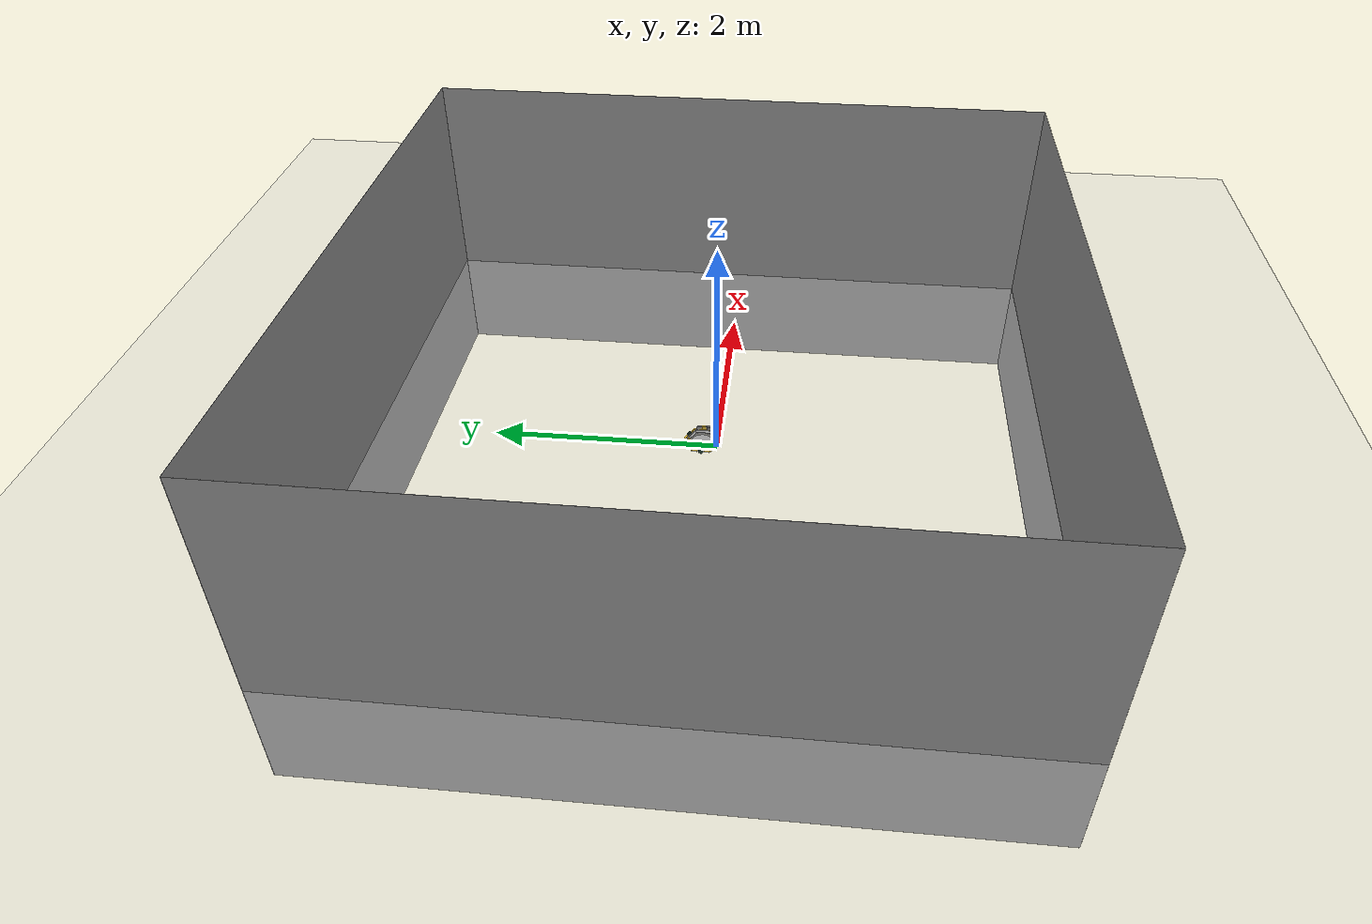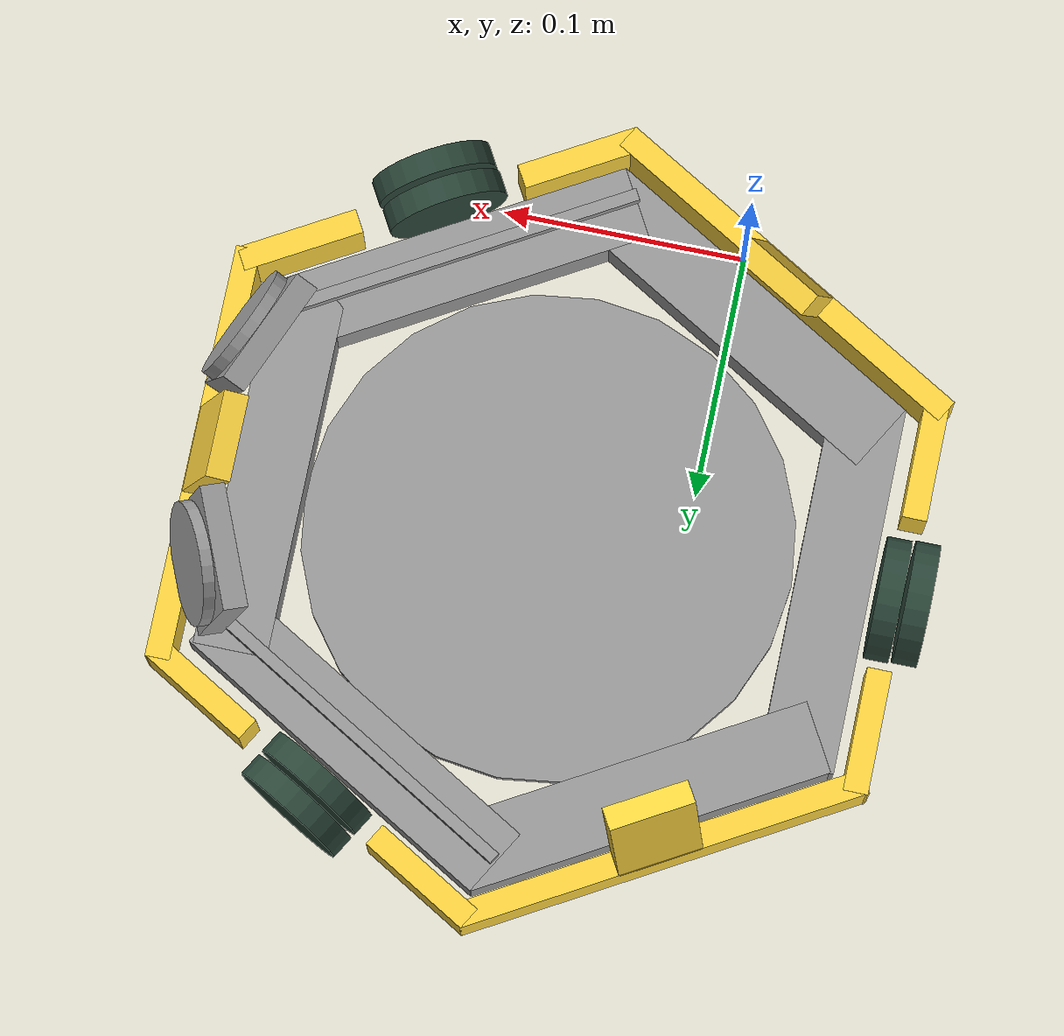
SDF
<sdf version="1.7">
 <world name="default">
  <model name="ground_plane">
   <static>1</static>
   <link name="link">
    <collision name="collision">
     <geometry><plane><normal>0 0 1</normal><size>100 100</size></plane></geometry>
     <surface>
      <contact><collide_bitmask>65535</collide_bitmask></contact>
      <friction><ode><mu>100</mu><mu2>50</mu2></ode></friction>
     </surface>
    </collision>
    <visual name="visual">
     <cast_shadows>0</cast_shadows>
     <geometry><plane><normal>0 0 1</normal><size>100 100</size></plane></geometry>
     <material>
      <script><uri>file://media/materials/scripts/gazebo.material</uri><name>Gazebo/Grey</name></script>
     </material>
    </visual>
   </link>
  </model>
  <light name="sun" type="directional">
   <pose>0 0 10 0 -0 0</pose>
   <diffuse>0.8 0.8 0.8 1</diffuse>
   <specular>0.2 0.2 0.2 1</specular>
   <attenuation>
    <range>1000</range>
    <constant>0.9</constant>
    <linear>0.01</linear>
    <quadratic>0.001</quadratic>
   </attenuation>
   <direction>-0.5 0.1 -0.9</direction>
   <spot><inner_angle>0</inner_angle><outer_angle>0</outer_angle><falloff>0</falloff></spot>
  </light>
  <gravity>0 0 -9.8</gravity>
  <magnetic_field>6e-06 2.3e-05 -4.2e-05</magnetic_field>
  <atmosphere type="adiabatic"/>
  <physics type="ode">
   <max_step_size>0.001</max_step_size>
   <real_time_factor>1</real_time_factor>
   <real_time_update_rate>1000</real_time_update_rate>
  </physics>
  <scene><ambient>0.4 0.4 0.4 1</ambient><background>0.7 0.7 0.7 1</background><shadows>1</shadows></scene>
  <spherical_coordinates>
   <surface_model>EARTH_WGS84</surface_model>
   <latitude_deg>0</latitude_deg>
   <longitude_deg>0</longitude_deg>
   <elevation>0</elevation>
   <heading_deg>0</heading_deg>
  </spherical_coordinates>
  <model name="Teo">
   <pose>0.054031 0.129721 -0.443502 1.3e-05 -1.4e-05 -0.000677</pose>
   <link name="hex_4">
    <inertial>
     <mass>1</mass>
     <inertia>
      <ixx>0.166667</ixx>
      <ixy>0</ixy>
      <ixz>0</ixz>
      <iyy>0.166667</iyy>
      <iyz>0</iyz>
      <izz>0.166667</izz>
     </inertia>
    </inertial>
    <pose>-0.115265 -4.6e-05 0.467464 0 -0 0</pose>
    <visual name="visual">
     <geometry><box><size>0.03 0.15 0.02</size></box></geometry>
     <material>
      <lighting>1</lighting>
      <script><uri>file://media/materials/scripts/gazebo.material</uri><name>Gazebo/Grey</name></script>
      <shader type="pixel"><normal_map>__default__</normal_map></shader>
      <ambient>0.564 0.56 0.556 1</ambient>
      <diffuse>0.7 0.7 0.7 1</diffuse>
      <specular>0.01 0.01 0.01 1</specular>
      <emissive>0 0 0 1</emissive>
     </material>
    </visual>
    <collision name="collision">
     <geometry><box><size>0.03 0.15 0.02</size></box></geometry>
     <surface>
      <friction>
       <ode><mu>1</mu><mu2>1</mu2><fdir1>0 0 0</fdir1><slip1>0</slip1><slip2>0</slip2></ode>
       <torsional>
        <coefficient>1</coefficient>
        <patch_radius>0</patch_radius>
        <surface_radius>0</surface_radius>
        <use_patch_radius>1</use_patch_radius>
        <ode><slip>0</slip></ode>
       </torsional>
      </friction>
      <bounce><restitution_coefficient>0</restitution_coefficient><threshold>1e+06</threshold></bounce>
      <contact>
       <collide_without_contact>0</collide_without_contact>
       <collide_without_contact_bitmask>1</collide_without_contact_bitmask>
       <collide_bitmask>1</collide_bitmask>
       <ode>
        <soft_cfm>0</soft_cfm>
        <soft_erp>0.2</soft_erp>
        <kp>1e+13</kp>
        <kd>1</kd>
        <max_vel>0.01</max_vel>
        <min_depth>0</min_depth>
       </ode>
       <bullet>
        <split_impulse>1</split_impulse>
        <split_impulse_penetration_threshold>-0.01</split_impulse_penetration_threshold>
        <soft_cfm>0</soft_cfm>
        <soft_erp>0.2</soft_erp>
        <kp>1e+13</kp>
        <kd>1</kd>
       </bullet>
      </contact>
     </surface>
    </collision>
   </link>
   <link name="cam_front">
    <inertial>
     <mass>1</mass>
     <inertia>
      <ixx>0.166667</ixx>
      <ixy>0</ixy>
      <ixz>0</ixz>
      <iyy>0.166667</iyy>
      <iyz>0</iyz>
      <izz>0.166667</izz>
     </inertia>
    </inertial>
    <pose>0.134968 -4.6e-05 0.506985 2.6e-05 1e-05 0</pose>
    <visual name="visual">
     <pose>0 0 0 0 -0.261799 0</pose>
     <geometry><box><size>0.01 0.035 0.05</size></box></geometry>
     <material>
      <lighting>1</lighting>
      <script><uri>file://media/materials/scripts/gazebo.material</uri><name>Gazebo/Grey</name></script>
      <shader type="pixel"><normal_map>__default__</normal_map></shader>
      <ambient>0.992 0.831 0.247 1</ambient>
      <diffuse>0.7 0.7 0.7 1</diffuse>
      <specular>0.01 0.01 0.01 1</specular>
      <emissive>0 0 0 1</emissive>
     </material>
    </visual>
    <collision name="collision">
     <pose>0 0 0 0 -0.261799 0</pose>
     <geometry><box><size>0.01 0.035 0.05</size></box></geometry>
     <surface>
      <friction>
       <ode><mu>1</mu><mu2>1</mu2><fdir1>0 0 0</fdir1><slip1>0</slip1><slip2>0</slip2></ode>
       <torsional>
        <coefficient>1</coefficient>
        <patch_radius>0</patch_radius>
        <surface_radius>0</surface_radius>
        <use_patch_radius>1</use_patch_radius>
        <ode><slip>0</slip></ode>
       </torsional>
      </friction>
      <bounce><restitution_coefficient>0</restitution_coefficient><threshold>1e+06</threshold></bounce>
      <contact>
       <collide_without_contact>0</collide_without_contact>
       <collide_without_contact_bitmask>1</collide_without_contact_bitmask>
       <collide_bitmask>1</collide_bitmask>
       <ode>
        <soft_cfm>0</soft_cfm>
        <soft_erp>0.2</soft_erp>
        <kp>1e+13</kp>
        <kd>1</kd>
        <max_vel>0.01</max_vel>
        <min_depth>0</min_depth>
       </ode>
       <bullet>
        <split_impulse>1</split_impulse>
        <split_impulse_penetration_threshold>-0.01</split_impulse_penetration_threshold>
        <soft_cfm>0</soft_cfm>
        <soft_erp>0.2</soft_erp>
        <kp>1e+13</kp>
        <kd>1</kd>
       </bullet>
      </contact>
     </surface>
    </collision>
   </link>
   <link name="cam_left">
    <inertial>
     <mass>1</mass>
     <inertia>
      <ixx>0.166667</ixx>
      <ixy>0</ixy>
      <ixz>0</ixz>
      <iyy>0.166667</iyy>
      <iyz>0</iyz>
      <izz>0.166667</izz>
     </inertia>
    </inertial>
    <pose>-0.064905 0.114347 0.506981 2.5e-05 -1e-05 -1e-05</pose>
    <visual name="visual">
     <pose>0 0 0 -0 -0.261799 2.0944</pose>
     <geometry><box><size>0.01 0.035 0.05</size></box></geometry>
     <material>
      <lighting>1</lighting>
      <script><uri>file://media/materials/scripts/gazebo.material</uri><name>Gazebo/Grey</name></script>
      <shader type="pixel"><normal_map>__default__</normal_map></shader>
      <ambient>0.992 0.831 0.247 1</ambient>
      <diffuse>0.7 0.7 0.7 1</diffuse>
      <specular>0.01 0.01 0.01 1</specular>
      <emissive>0 0 0 1</emissive>
     </material>
    </visual>
    <collision name="collision">
     <pose>0 0 0 -0 -0.261799 2.0944</pose>
     <geometry><box><size>0.01 0.035 0.05</size></box></geometry>
     <surface>
      <friction>
       <ode><mu>1</mu><mu2>1</mu2><fdir1>0 0 0</fdir1><slip1>0</slip1><slip2>0</slip2></ode>
       <torsional>
        <coefficient>1</coefficient>
        <patch_radius>0</patch_radius>
        <surface_radius>0</surface_radius>
        <use_patch_radius>1</use_patch_radius>
        <ode><slip>0</slip></ode>
       </torsional>
      </friction>
      <bounce><restitution_coefficient>0</restitution_coefficient><threshold>1e+06</threshold></bounce>
      <contact>
       <collide_without_contact>0</collide_without_contact>
       <collide_without_contact_bitmask>1</collide_without_contact_bitmask>
       <collide_bitmask>1</collide_bitmask>
       <ode>
        <soft_cfm>0</soft_cfm>
        <soft_erp>0.2</soft_erp>
        <kp>1e+13</kp>
        <kd>1</kd>
        <max_vel>0.01</max_vel>
        <min_depth>0</min_depth>
       </ode>
       <bullet>
        <split_impulse>1</split_impulse>
        <split_impulse_penetration_threshold>-0.01</split_impulse_penetration_threshold>
        <soft_cfm>0</soft_cfm>
        <soft_erp>0.2</soft_erp>
        <kp>1e+13</kp>
        <kd>1</kd>
       </bullet>
      </contact>
     </surface>
    </collision>
   </link>
   <link name="cam_right">
    <inertial>
     <mass>1</mass>
     <inertia>
      <ixx>0.166667</ixx>
      <ixy>0</ixy>
      <ixz>0</ixz>
      <iyy>0.166667</iyy>
      <iyz>0</iyz>
      <izz>0.166667</izz>
     </inertia>
    </inertial>
    <pose>-0.072039 -0.11163 0.506985 2.5e-05 -1e-05 -1e-05</pose>
    <visual name="visual">
     <pose>0 0 0 0 0.261799 1.0472</pose>
     <geometry><box><size>0.01 0.035 0.05</size></box></geometry>
     <material>
      <lighting>1</lighting>
      <script><uri>file://media/materials/scripts/gazebo.material</uri><name>Gazebo/Grey</name></script>
      <shader type="pixel"><normal_map>__default__</normal_map></shader>
      <ambient>0.992 0.831 0.247 1</ambient>
      <diffuse>0.7 0.7 0.7 1</diffuse>
      <specular>0.01 0.01 0.01 1</specular>
      <emissive>0 0 0 1</emissive>
     </material>
    </visual>
    <collision name="collision">
     <pose>0 0 0 0 0.261799 1.0472</pose>
     <geometry><box><size>0.01 0.035 0.05</size></box></geometry>
     <surface>
      <friction>
       <ode><mu>1</mu><mu2>1</mu2><fdir1>0 0 0</fdir1><slip1>0</slip1><slip2>0</slip2></ode>
       <torsional>
        <coefficient>1</coefficient>
        <patch_radius>0</patch_radius>
        <surface_radius>0</surface_radius>
        <use_patch_radius>1</use_patch_radius>
        <ode><slip>0</slip></ode>
       </torsional>
      </friction>
      <bounce><restitution_coefficient>0</restitution_coefficient><threshold>1e+06</threshold></bounce>
      <contact>
       <collide_without_contact>0</collide_without_contact>
       <collide_without_contact_bitmask>1</collide_without_contact_bitmask>
       <collide_bitmask>1</collide_bitmask>
       <ode>
        <soft_cfm>0</soft_cfm>
        <soft_erp>0.2</soft_erp>
        <kp>1e+13</kp>
        <kd>1</kd>
        <max_vel>0.01</max_vel>
        <min_depth>0</min_depth>
       </ode>
       <bullet>
        <split_impulse>1</split_impulse>
        <split_impulse_penetration_threshold>-0.01</split_impulse_penetration_threshold>
        <soft_cfm>0</soft_cfm>
        <soft_erp>0.2</soft_erp>
        <kp>1e+13</kp>
        <kd>1</kd>
       </bullet>
      </contact>
     </surface>
    </collision>
   </link>
   <link name="hex_1">
    <inertial>
     <mass>1</mass>
     <inertia>
      <ixx>0.166667</ixx>
      <ixy>0</ixy>
      <ixz>0</ixz>
      <iyy>0.166667</iyy>
      <iyz>0</iyz>
      <izz>0.166667</izz>
     </inertia>
    </inertial>
    <pose>0.114365 -4.6e-05 0.467468 0 -0 0</pose>
    <visual name="visual">
     <geometry><box><size>0.03 0.15 0.02</size></box></geometry>
     <material>
      <lighting>1</lighting>
      <script><uri>file://media/materials/scripts/gazebo.material</uri><name>Gazebo/Grey</name></script>
      <shader type="pixel"><normal_map>__default__</normal_map></shader>
      <ambient>0.564 0.56 0.556 1</ambient>
      <diffuse>0.7 0.7 0.7 1</diffuse>
      <specular>0.01 0.01 0.01 1</specular>
      <emissive>0 0 0 1</emissive>
     </material>
    </visual>
    <collision name="collision">
     <geometry><box><size>0.03 0.15 0.02</size></box></geometry>
     <surface>
      <friction>
       <ode><mu>1</mu><mu2>1</mu2><fdir1>0 0 0</fdir1><slip1>0</slip1><slip2>0</slip2></ode>
       <torsional>
        <coefficient>1</coefficient>
        <patch_radius>0</patch_radius>
        <surface_radius>0</surface_radius>
        <use_patch_radius>1</use_patch_radius>
        <ode><slip>0</slip></ode>
       </torsional>
      </friction>
      <bounce><restitution_coefficient>0</restitution_coefficient><threshold>1e+06</threshold></bounce>
      <contact>
       <collide_without_contact>0</collide_without_contact>
       <collide_without_contact_bitmask>1</collide_without_contact_bitmask>
       <collide_bitmask>1</collide_bitmask>
       <ode>
        <soft_cfm>0</soft_cfm>
        <soft_erp>0.2</soft_erp>
        <kp>1e+13</kp>
        <kd>1</kd>
        <max_vel>0.01</max_vel>
        <min_depth>0</min_depth>
       </ode>
       <bullet>
        <split_impulse>1</split_impulse>
        <split_impulse_penetration_threshold>-0.01</split_impulse_penetration_threshold>
        <soft_cfm>0</soft_cfm>
        <soft_erp>0.2</soft_erp>
        <kp>1e+13</kp>
        <kd>1</kd>
       </bullet>
      </contact>
     </surface>
    </collision>
   </link>
   <link name="hex_2">
    <inertial>
     <mass>1</mass>
     <inertia>
      <ixx>0.166667</ixx>
      <ixy>0</ixy>
      <ixz>0</ixz>
      <iyy>0.166667</iyy>
      <iyz>0</iyz>
      <izz>0.166667</izz>
     </inertia>
    </inertial>
    <pose>0.057316 -0.099273 0.467468 0 -0 0</pose>
    <visual name="visual">
     <pose>0 0 0 0 -0 2.0944</pose>
     <geometry><box><size>0.03 0.15 0.02</size></box></geometry>
     <material>
      <lighting>1</lighting>
      <script><uri>file://media/materials/scripts/gazebo.material</uri><name>Gazebo/Grey</name></script>
      <shader type="pixel"><normal_map>__default__</normal_map></shader>
      <ambient>0.564 0.56 0.556 1</ambient>
      <diffuse>0.7 0.7 0.7 1</diffuse>
      <specular>0.01 0.01 0.01 1</specular>
      <emissive>0 0 0 1</emissive>
     </material>
    </visual>
    <collision name="collision">
     <pose>0 0 0 0 -0 2.0944</pose>
     <geometry><box><size>0.03 0.15 0.02</size></box></geometry>
     <surface>
      <friction>
       <ode><mu>1</mu><mu2>1</mu2><fdir1>0 0 0</fdir1><slip1>0</slip1><slip2>0</slip2></ode>
       <torsional>
        <coefficient>1</coefficient>
        <patch_radius>0</patch_radius>
        <surface_radius>0</surface_radius>
        <use_patch_radius>1</use_patch_radius>
        <ode><slip>0</slip></ode>
       </torsional>
      </friction>
      <bounce><restitution_coefficient>0</restitution_coefficient><threshold>1e+06</threshold></bounce>
      <contact>
       <collide_without_contact>0</collide_without_contact>
       <collide_without_contact_bitmask>1</collide_without_contact_bitmask>
       <collide_bitmask>1</collide_bitmask>
       <ode>
        <soft_cfm>0</soft_cfm>
        <soft_erp>0.2</soft_erp>
        <kp>1e+13</kp>
        <kd>1</kd>
        <max_vel>0.01</max_vel>
        <min_depth>0</min_depth>
       </ode>
       <bullet>
        <split_impulse>1</split_impulse>
        <split_impulse_penetration_threshold>-0.01</split_impulse_penetration_threshold>
        <soft_cfm>0</soft_cfm>
        <soft_erp>0.2</soft_erp>
        <kp>1e+13</kp>
        <kd>1</kd>
       </bullet>
      </contact>
     </surface>
    </collision>
   </link>
   <link name="hex_3">
    <inertial>
     <mass>1</mass>
     <inertia>
      <ixx>0.166667</ixx>
      <ixy>0</ixy>
      <ixz>0</ixz>
      <iyy>0.166667</iyy>
      <iyz>0</iyz>
      <izz>0.166667</izz>
     </inertia>
    </inertial>
    <pose>-0.057561 -0.099494 0.467466 0 -0 0</pose>
    <visual name="visual">
     <pose>0 0 0 0 -0 1.0472</pose>
     <geometry><box><size>0.03 0.15 0.02</size></box></geometry>
     <material>
      <lighting>1</lighting>
      <script><uri>file://media/materials/scripts/gazebo.material</uri><name>Gazebo/Grey</name></script>
      <shader type="pixel"><normal_map>__default__</normal_map></shader>
      <ambient>0.564 0.56 0.556 1</ambient>
      <diffuse>0.7 0.7 0.7 1</diffuse>
      <specular>0.01 0.01 0.01 1</specular>
      <emissive>0 0 0 1</emissive>
     </material>
    </visual>
    <collision name="collision">
     <pose>0 0 0 0 -0 1.0472</pose>
     <geometry><box><size>0.03 0.15 0.02</size></box></geometry>
     <surface>
      <friction>
       <ode><mu>1</mu><mu2>1</mu2><fdir1>0 0 0</fdir1><slip1>0</slip1><slip2>0</slip2></ode>
       <torsional>
        <coefficient>1</coefficient>
        <patch_radius>0</patch_radius>
        <surface_radius>0</surface_radius>
        <use_patch_radius>1</use_patch_radius>
        <ode><slip>0</slip></ode>
       </torsional>
      </friction>
      <bounce><restitution_coefficient>0</restitution_coefficient><threshold>1e+06</threshold></bounce>
      <contact>
       <collide_without_contact>0</collide_without_contact>
       <collide_without_contact_bitmask>1</collide_without_contact_bitmask>
       <collide_bitmask>1</collide_bitmask>
       <ode>
        <soft_cfm>0</soft_cfm>
        <soft_erp>0.2</soft_erp>
        <kp>1e+13</kp>
        <kd>1</kd>
        <max_vel>0.01</max_vel>
        <min_depth>0</min_depth>
       </ode>
       <bullet>
        <split_impulse>1</split_impulse>
        <split_impulse_penetration_threshold>-0.01</split_impulse_penetration_threshold>
        <soft_cfm>0</soft_cfm>
        <soft_erp>0.2</soft_erp>
        <kp>1e+13</kp>
        <kd>1</kd>
       </bullet>
      </contact>
     </surface>
    </collision>
   </link>
   <link name="hex_5">
    <inertial>
     <mass>1</mass>
     <inertia>
      <ixx>0.166667</ixx>
      <ixy>0</ixy>
      <ixz>0</ixz>
      <iyy>0.166667</iyy>
      <iyz>0</iyz>
      <izz>0.166667</izz>
     </inertia>
    </inertial>
    <pose>-0.05671 0.099096 0.467466 0 -0 0</pose>
    <visual name="visual">
     <pose>0 0 0 0 -0 2.0944</pose>
     <geometry><box><size>0.03 0.15 0.02</size></box></geometry>
     <material>
      <lighting>1</lighting>
      <script><uri>file://media/materials/scripts/gazebo.material</uri><name>Gazebo/Grey</name></script>
      <shader type="pixel"><normal_map>__default__</normal_map></shader>
      <ambient>0.564 0.56 0.556 1</ambient>
      <diffuse>0.7 0.7 0.7 1</diffuse>
      <specular>0.01 0.01 0.01 1</specular>
      <emissive>0 0 0 1</emissive>
     </material>
    </visual>
    <collision name="collision">
     <pose>0 0 0 0 -0 2.0944</pose>
     <geometry><box><size>0.03 0.15 0.02</size></box></geometry>
     <surface>
      <friction>
       <ode><mu>1</mu><mu2>1</mu2><fdir1>0 0 0</fdir1><slip1>0</slip1><slip2>0</slip2></ode>
       <torsional>
        <coefficient>1</coefficient>
        <patch_radius>0</patch_radius>
        <surface_radius>0</surface_radius>
        <use_patch_radius>1</use_patch_radius>
        <ode><slip>0</slip></ode>
       </torsional>
      </friction>
      <bounce><restitution_coefficient>0</restitution_coefficient><threshold>1e+06</threshold></bounce>
      <contact>
       <collide_without_contact>0</collide_without_contact>
       <collide_without_contact_bitmask>1</collide_without_contact_bitmask>
       <collide_bitmask>1</collide_bitmask>
       <ode>
        <soft_cfm>0</soft_cfm>
        <soft_erp>0.2</soft_erp>
        <kp>1e+13</kp>
        <kd>1</kd>
        <max_vel>0.01</max_vel>
        <min_depth>0</min_depth>
       </ode>
       <bullet>
        <split_impulse>1</split_impulse>
        <split_impulse_penetration_threshold>-0.01</split_impulse_penetration_threshold>
        <soft_cfm>0</soft_cfm>
        <soft_erp>0.2</soft_erp>
        <kp>1e+13</kp>
        <kd>1</kd>
       </bullet>
      </contact>
     </surface>
    </collision>
   </link>
   <link name="hex_6">
    <inertial>
     <mass>1</mass>
     <inertia>
      <ixx>0.166667</ixx>
      <ixy>0</ixy>
      <ixz>0</ixz>
      <iyy>0.166667</iyy>
      <iyz>0</iyz>
      <izz>0.166667</izz>
     </inertia>
    </inertial>
    <pose>0.05861 0.099149 0.467468 0 -0 0</pose>
    <visual name="visual">
     <pose>0 0 0 0 -0 1.0472</pose>
     <geometry><box><size>0.03 0.15 0.02</size></box></geometry>
     <material>
      <lighting>1</lighting>
      <script><uri>file://media/materials/scripts/gazebo.material</uri><name>Gazebo/Grey</name></script>
      <shader type="pixel"><normal_map>__default__</normal_map></shader>
      <ambient>0.564 0.56 0.556 1</ambient>
      <diffuse>0.7 0.7 0.7 1</diffuse>
      <specular>0.01 0.01 0.01 1</specular>
      <emissive>0 0 0 1</emissive>
     </material>
    </visual>
    <collision name="collision">
     <pose>0 0 0 0 -0 1.0472</pose>
     <geometry><box><size>0.03 0.15 0.02</size></box></geometry>
     <surface>
      <friction>
       <ode><mu>1</mu><mu2>1</mu2><fdir1>0 0 0</fdir1><slip1>0</slip1><slip2>0</slip2></ode>
       <torsional>
        <coefficient>1</coefficient>
        <patch_radius>0</patch_radius>
        <surface_radius>0</surface_radius>
        <use_patch_radius>1</use_patch_radius>
        <ode><slip>0</slip></ode>
       </torsional>
      </friction>
      <bounce><restitution_coefficient>0</restitution_coefficient><threshold>1e+06</threshold></bounce>
      <contact>
       <collide_without_contact>0</collide_without_contact>
       <collide_without_contact_bitmask>1</collide_without_contact_bitmask>
       <collide_bitmask>1</collide_bitmask>
       <ode>
        <soft_cfm>0</soft_cfm>
        <soft_erp>0.2</soft_erp>
        <kp>1e+13</kp>
        <kd>1</kd>
        <max_vel>0.01</max_vel>
        <min_depth>0</min_depth>
       </ode>
       <bullet>
        <split_impulse>1</split_impulse>
        <split_impulse_penetration_threshold>-0.01</split_impulse_penetration_threshold>
        <soft_cfm>0</soft_cfm>
        <soft_erp>0.2</soft_erp>
        <kp>1e+13</kp>
        <kd>1</kd>
       </bullet>
      </contact>
     </surface>
    </collision>
   </link>
   <link name="hex_base">
    <inertial>
     <mass>1</mass>
     <inertia><ixx>0.145833</ixx><ixy>0</ixy><ixz>0</ixz><iyy>0.145833</iyy><iyz>0</iyz><izz>0.125</izz></inertia>
    </inertial>
    <pose>0.00059 0.000329 0.451295 0 -0 0</pose>
    <visual name="visual">
     <geometry><cylinder><radius>0.1</radius><length>0.005</length></cylinder></geometry>
     <material>
      <lighting>1</lighting>
      <script><uri>file://media/materials/scripts/gazebo.material</uri><name>Gazebo/Grey</name></script>
      <shader type="pixel"><normal_map>__default__</normal_map></shader>
      <ambient>0.564 0.56 0.556 1</ambient>
      <diffuse>0.7 0.7 0.7 1</diffuse>
      <specular>0.01 0.01 0.01 1</specular>
      <emissive>0 0 0 1</emissive>
     </material>
    </visual>
    <collision name="collision">
     <geometry><cylinder><radius>0.1</radius><length>0.005</length></cylinder></geometry>
     <surface>
      <friction>
       <ode><mu>1</mu><mu2>1</mu2><fdir1>0 0 0</fdir1><slip1>0</slip1><slip2>0</slip2></ode>
       <torsional>
        <coefficient>1</coefficient>
        <patch_radius>0</patch_radius>
        <surface_radius>0</surface_radius>
        <use_patch_radius>1</use_patch_radius>
        <ode><slip>0</slip></ode>
       </torsional>
      </friction>
      <bounce><restitution_coefficient>0</restitution_coefficient><threshold>1e+06</threshold></bounce>
      <contact>
       <collide_without_contact>0</collide_without_contact>
       <collide_without_contact_bitmask>1</collide_without_contact_bitmask>
       <collide_bitmask>1</collide_bitmask>
       <ode>
        <soft_cfm>0</soft_cfm>
        <soft_erp>0.2</soft_erp>
        <kp>1e+13</kp>
        <kd>1</kd>
        <max_vel>0.01</max_vel>
        <min_depth>0</min_depth>
       </ode>
       <bullet>
        <split_impulse>1</split_impulse>
        <split_impulse_penetration_threshold>-0.01</split_impulse_penetration_threshold>
        <soft_cfm>0</soft_cfm>
        <soft_erp>0.2</soft_erp>
        <kp>1e+13</kp>
        <kd>1</kd>
       </bullet>
      </contact>
     </surface>
    </collision>
   </link>
   <link name="led_left">
    <inertial>
     <mass>1</mass>
     <inertia>
      <ixx>0.166667</ixx>
      <ixy>0</ixy>
      <ixz>0</ixz>
      <iyy>0.166667</iyy>
      <iyz>0</iyz>
      <izz>0.166667</izz>
     </inertia>
    </inertial>
    <pose>0.05861 0.099149 0.489855 -2e-06 -4e-05 -2e-05</pose>
    <light name="light_source_left" type="point">
     <attenuation><range>0</range><linear>0</linear><constant>0</constant></attenuation>
     <diffuse>1 0 0 1</diffuse>
     <specular>1 0 0 1</specular>
     <direction>0 0 -1</direction>
     <spot><inner_angle>0</inner_angle><outer_angle>0</outer_angle><falloff>0</falloff></spot>
     <ambient>1 0 0 1</ambient>
    </light>
    <visual name="visual">
     <pose>0 0 0 0 0 -2.0944</pose>
     <geometry><box><size>0.005 0.15 0.005</size></box></geometry>
     <material>
      <lighting>1</lighting>
      <script><uri>file://media/materials/scripts/gazebo.material</uri><name>Gazebo/Grey</name></script>
      <shader type="pixel"><normal_map>__default__</normal_map></shader>
      <ambient>0.564 0.56 0.556 1</ambient>
      <diffuse>0.7 0.7 0.7 1</diffuse>
      <specular>0.01 0.01 0.01 1</specular>
      <emissive>0 0 0 1</emissive>
     </material>
    </visual>
    <collision name="collision">
     <pose>0 0 0 0 0 -2.0944</pose>
     <geometry><box><size>0.005 0.15 0.005</size></box></geometry>
     <surface>
      <friction>
       <ode><mu>1</mu><mu2>1</mu2><fdir1>0 0 0</fdir1><slip1>0</slip1><slip2>0</slip2></ode>
       <torsional>
        <coefficient>1</coefficient>
        <patch_radius>0</patch_radius>
        <surface_radius>0</surface_radius>
        <use_patch_radius>1</use_patch_radius>
        <ode><slip>0</slip></ode>
       </torsional>
      </friction>
      <bounce><restitution_coefficient>0</restitution_coefficient><threshold>1e+06</threshold></bounce>
      <contact>
       <collide_without_contact>0</collide_without_contact>
       <collide_without_contact_bitmask>1</collide_without_contact_bitmask>
       <collide_bitmask>1</collide_bitmask>
       <ode>
        <soft_cfm>0</soft_cfm>
        <soft_erp>0.2</soft_erp>
        <kp>1e+13</kp>
        <kd>1</kd>
        <max_vel>0.01</max_vel>
        <min_depth>0</min_depth>
       </ode>
       <bullet>
        <split_impulse>1</split_impulse>
        <split_impulse_penetration_threshold>-0.01</split_impulse_penetration_threshold>
        <soft_cfm>0</soft_cfm>
        <soft_erp>0.2</soft_erp>
        <kp>1e+13</kp>
        <kd>1</kd>
       </bullet>
      </contact>
     </surface>
    </collision>
   </link>
   <link name="led_right">
    <inertial>
     <mass>1</mass>
     <inertia>
      <ixx>0.166667</ixx>
      <ixy>0</ixy>
      <ixz>0</ixz>
      <iyy>0.166667</iyy>
      <iyz>0</iyz>
      <izz>0.166667</izz>
     </inertia>
    </inertial>
    <pose>0.057316 -0.099273 0.489854 -1e-06 -2e-05 -1e-05</pose>
    <light name="light_source_right" type="point">
     <attenuation><range>0</range><linear>0</linear><constant>0</constant></attenuation>
     <diffuse>1 0 0 1</diffuse>
     <specular>1 0 0 1</specular>
     <direction>0 0 -1</direction>
     <spot><inner_angle>0</inner_angle><outer_angle>0</outer_angle><falloff>0</falloff></spot>
     <ambient>1 0 0 1</ambient>
    </light>
    <visual name="visual">
     <pose>0 0 0 0 -0 2.0944</pose>
     <geometry><box><size>0.005 0.15 0.005</size></box></geometry>
     <material>
      <lighting>1</lighting>
      <script><uri>file://media/materials/scripts/gazebo.material</uri><name>Gazebo/Grey</name></script>
      <shader type="pixel"><normal_map>__default__</normal_map></shader>
      <ambient>0.564 0.56 0.556 1</ambient>
      <diffuse>0.7 0.7 0.7 1</diffuse>
      <specular>0.01 0.01 0.01 1</specular>
      <emissive>0 0 0 1</emissive>
     </material>
    </visual>
    <collision name="collision">
     <pose>0 0 0 0 -0 2.0944</pose>
     <geometry><box><size>0.005 0.15 0.005</size></box></geometry>
     <surface>
      <friction>
       <ode><mu>1</mu><mu2>1</mu2><fdir1>0 0 0</fdir1><slip1>0</slip1><slip2>0</slip2></ode>
       <torsional>
        <coefficient>1</coefficient>
        <patch_radius>0</patch_radius>
        <surface_radius>0</surface_radius>
        <use_patch_radius>1</use_patch_radius>
        <ode><slip>0</slip></ode>
       </torsional>
      </friction>
      <bounce><restitution_coefficient>0</restitution_coefficient><threshold>1e+06</threshold></bounce>
      <contact>
       <collide_without_contact>0</collide_without_contact>
       <collide_without_contact_bitmask>1</collide_without_contact_bitmask>
       <collide_bitmask>1</collide_bitmask>
       <ode>
        <soft_cfm>0</soft_cfm>
        <soft_erp>0.2</soft_erp>
        <kp>1e+13</kp>
        <kd>1</kd>
        <max_vel>0.01</max_vel>
        <min_depth>0</min_depth>
       </ode>
       <bullet>
        <split_impulse>1</split_impulse>
        <split_impulse_penetration_threshold>-0.01</split_impulse_penetration_threshold>
        <soft_cfm>0</soft_cfm>
        <soft_erp>0.2</soft_erp>
        <kp>1e+13</kp>
        <kd>1</kd>
       </bullet>
      </contact>
     </surface>
    </collision>
   </link>
   <link name="shl_1">
    <inertial>
     <mass>1</mass>
     <inertia>
      <ixx>0.166667</ixx>
      <ixy>0</ixy>
      <ixz>0</ixz>
      <iyy>0.166667</iyy>
      <iyz>0</iyz>
      <izz>0.166667</izz>
     </inertia>
    </inertial>
    <pose>0.141189 -4.6e-05 0.470406 1.3e-05 5e-06 0</pose>
    <visual name="visual">
     <geometry><box><size>0.01 0.17 0.03</size></box></geometry>
     <material>
      <lighting>1</lighting>
      <script><uri>file://media/materials/scripts/gazebo.material</uri><name>Gazebo/Grey</name></script>
      <shader type="pixel"><normal_map>__default__</normal_map></shader>
      <ambient>0.992 0.831 0.247 1</ambient>
      <diffuse>0.7 0.7 0.7 1</diffuse>
      <specular>0.01 0.01 0.01 1</specular>
      <emissive>0 0 0 1</emissive>
     </material>
    </visual>
    <collision name="collision">
     <geometry><box><size>0.01 0.17 0.03</size></box></geometry>
     <surface>
      <friction>
       <ode><mu>1</mu><mu2>1</mu2><fdir1>0 0 0</fdir1><slip1>0</slip1><slip2>0</slip2></ode>
       <torsional>
        <coefficient>1</coefficient>
        <patch_radius>0</patch_radius>
        <surface_radius>0</surface_radius>
        <use_patch_radius>1</use_patch_radius>
        <ode><slip>0</slip></ode>
       </torsional>
      </friction>
      <bounce><restitution_coefficient>0</restitution_coefficient><threshold>1e+06</threshold></bounce>
      <contact>
       <collide_without_contact>0</collide_without_contact>
       <collide_without_contact_bitmask>1</collide_without_contact_bitmask>
       <collide_bitmask>1</collide_bitmask>
       <ode>
        <soft_cfm>0</soft_cfm>
        <soft_erp>0.2</soft_erp>
        <kp>1e+13</kp>
        <kd>1</kd>
        <max_vel>0.01</max_vel>
        <min_depth>0</min_depth>
       </ode>
       <bullet>
        <split_impulse>1</split_impulse>
        <split_impulse_penetration_threshold>-0.01</split_impulse_penetration_threshold>
        <soft_cfm>0</soft_cfm>
        <soft_erp>0.2</soft_erp>
        <kp>1e+13</kp>
        <kd>1</kd>
       </bullet>
      </contact>
     </surface>
    </collision>
   </link>
   <link name="shl_2">
    <inertial>
     <mass>1</mass>
     <inertia>
      <ixx>0.166667</ixx>
      <ixy>0</ixy>
      <ixz>0</ixz>
      <iyy>0.166667</iyy>
      <iyz>0</iyz>
      <izz>0.166667</izz>
     </inertia>
    </inertial>
    <pose>0.121568 -0.092422 0.470405 3.9e-05 1.5e-05 0</pose>
    <visual name="visual">
     <pose>0 0 0 0 -0 2.0944</pose>
     <geometry><box><size>0.01 0.05 0.03</size></box></geometry>
     <material>
      <lighting>1</lighting>
      <script><uri>file://media/materials/scripts/gazebo.material</uri><name>Gazebo/Grey</name></script>
      <shader type="pixel"><normal_map>__default__</normal_map></shader>
      <ambient>0.992 0.831 0.247 1</ambient>
      <diffuse>0.7 0.7 0.7 1</diffuse>
      <specular>0.01 0.01 0.01 1</specular>
      <emissive>0 0 0 1</emissive>
     </material>
    </visual>
    <collision name="collision">
     <pose>0 0 0 0 -0 2.0944</pose>
     <geometry><box><size>0.01 0.05 0.03</size></box></geometry>
     <surface>
      <friction>
       <ode><mu>1</mu><mu2>1</mu2><fdir1>0 0 0</fdir1><slip1>0</slip1><slip2>0</slip2></ode>
       <torsional>
        <coefficient>1</coefficient>
        <patch_radius>0</patch_radius>
        <surface_radius>0</surface_radius>
        <use_patch_radius>1</use_patch_radius>
        <ode><slip>0</slip></ode>
       </torsional>
      </friction>
      <bounce><restitution_coefficient>0</restitution_coefficient><threshold>1e+06</threshold></bounce>
      <contact>
       <collide_without_contact>0</collide_without_contact>
       <collide_without_contact_bitmask>1</collide_without_contact_bitmask>
       <collide_bitmask>1</collide_bitmask>
       <ode>
        <soft_cfm>0</soft_cfm>
        <soft_erp>0.2</soft_erp>
        <kp>1e+13</kp>
        <kd>1</kd>
        <max_vel>0.01</max_vel>
        <min_depth>0</min_depth>
       </ode>
       <bullet>
        <split_impulse>1</split_impulse>
        <split_impulse_penetration_threshold>-0.01</split_impulse_penetration_threshold>
        <soft_cfm>0</soft_cfm>
        <soft_erp>0.2</soft_erp>
        <kp>1e+13</kp>
        <kd>1</kd>
       </bullet>
      </contact>
     </surface>
    </collision>
   </link>
   <link name="shl_3">
    <inertial>
     <mass>1</mass>
     <inertia>
      <ixx>0.166667</ixx>
      <ixy>0</ixy>
      <ixz>0</ixz>
      <iyy>0.166667</iyy>
      <iyz>0</iyz>
      <izz>0.166667</izz>
     </inertia>
    </inertial>
    <pose>0.0182 -0.14851 0.470406 3.8e-05 -5e-06 -1e-05</pose>
    <visual name="visual">
     <pose>0 0 0 0 -0 2.0944</pose>
     <geometry><box><size>0.01 0.05 0.03</size></box></geometry>
     <material>
      <lighting>1</lighting>
      <script><uri>file://media/materials/scripts/gazebo.material</uri><name>Gazebo/Grey</name></script>
      <shader type="pixel"><normal_map>__default__</normal_map></shader>
      <ambient>0.992 0.831 0.247 1</ambient>
      <diffuse>0.7 0.7 0.7 1</diffuse>
      <specular>0.01 0.01 0.01 1</specular>
      <emissive>0 0 0 1</emissive>
     </material>
    </visual>
    <collision name="collision">
     <pose>0 0 0 0 -0 2.0944</pose>
     <geometry><box><size>0.01 0.05 0.03</size></box></geometry>
     <surface>
      <friction>
       <ode><mu>1</mu><mu2>1</mu2><fdir1>0 0 0</fdir1><slip1>0</slip1><slip2>0</slip2></ode>
       <torsional>
        <coefficient>1</coefficient>
        <patch_radius>0</patch_radius>
        <surface_radius>0</surface_radius>
        <use_patch_radius>1</use_patch_radius>
        <ode><slip>0</slip></ode>
       </torsional>
      </friction>
      <bounce><restitution_coefficient>0</restitution_coefficient><threshold>1e+06</threshold></bounce>
      <contact>
       <collide_without_contact>0</collide_without_contact>
       <collide_without_contact_bitmask>1</collide_without_contact_bitmask>
       <collide_bitmask>1</collide_bitmask>
       <ode>
        <soft_cfm>0</soft_cfm>
        <soft_erp>0.2</soft_erp>
        <kp>1e+13</kp>
        <kd>1</kd>
        <max_vel>0.01</max_vel>
        <min_depth>0</min_depth>
       </ode>
       <bullet>
        <split_impulse>1</split_impulse>
        <split_impulse_penetration_threshold>-0.01</split_impulse_penetration_threshold>
        <soft_cfm>0</soft_cfm>
        <soft_erp>0.2</soft_erp>
        <kp>1e+13</kp>
        <kd>1</kd>
       </bullet>
      </contact>
     </surface>
    </collision>
   </link>
   <link name="shl_4">
    <inertial>
     <mass>1</mass>
     <inertia>
      <ixx>0.166667</ixx>
      <ixy>0</ixy>
      <ixz>0</ixz>
      <iyy>0.166667</iyy>
      <iyz>0</iyz>
      <izz>0.166667</izz>
     </inertia>
    </inertial>
    <pose>-0.0723 -0.118648 0.470405 1.1e-05 -3.5e-05 -2e-05</pose>
    <visual name="visual">
     <pose>0 0 0 0 -0 1.0472</pose>
     <geometry><box><size>0.01 0.17 0.03</size></box></geometry>
     <material>
      <lighting>1</lighting>
      <script><uri>file://media/materials/scripts/gazebo.material</uri><name>Gazebo/Grey</name></script>
      <shader type="pixel"><normal_map>__default__</normal_map></shader>
      <ambient>0.992 0.831 0.247 1</ambient>
      <diffuse>0.7 0.7 0.7 1</diffuse>
      <specular>0.01 0.01 0.01 1</specular>
      <emissive>0 0 0 1</emissive>
     </material>
    </visual>
    <collision name="collision">
     <pose>0 0 0 0 -0 1.0472</pose>
     <geometry><box><size>0.01 0.17 0.03</size></box></geometry>
     <surface>
      <friction>
       <ode><mu>1</mu><mu2>1</mu2><fdir1>0 0 0</fdir1><slip1>0</slip1><slip2>0</slip2></ode>
       <torsional>
        <coefficient>1</coefficient>
        <patch_radius>0</patch_radius>
        <surface_radius>0</surface_radius>
        <use_patch_radius>1</use_patch_radius>
        <ode><slip>0</slip></ode>
       </torsional>
      </friction>
      <bounce><restitution_coefficient>0</restitution_coefficient><threshold>1e+06</threshold></bounce>
      <contact>
       <collide_without_contact>0</collide_without_contact>
       <collide_without_contact_bitmask>1</collide_without_contact_bitmask>
       <collide_bitmask>1</collide_bitmask>
       <ode>
        <soft_cfm>0</soft_cfm>
        <soft_erp>0.2</soft_erp>
        <kp>1e+13</kp>
        <kd>1</kd>
        <max_vel>0.01</max_vel>
        <min_depth>0</min_depth>
       </ode>
       <bullet>
        <split_impulse>1</split_impulse>
        <split_impulse_penetration_threshold>-0.01</split_impulse_penetration_threshold>
        <soft_cfm>0</soft_cfm>
        <soft_erp>0.2</soft_erp>
        <kp>1e+13</kp>
        <kd>1</kd>
       </bullet>
      </contact>
     </surface>
    </collision>
   </link>
   <link name="shl_5">
    <inertial>
     <mass>1</mass>
     <inertia>
      <ixx>0.166667</ixx>
      <ixy>0</ixy>
      <ixz>0</ixz>
      <iyy>0.166667</iyy>
      <iyz>0</iyz>
      <izz>0.166667</izz>
     </inertia>
    </inertial>
    <pose>-0.141741 -0.0558 0.470403 2.5e-05 -1e-05 -1e-05</pose>
    <visual name="visual">
     <geometry><box><size>0.01 0.05 0.03</size></box></geometry>
     <material>
      <lighting>1</lighting>
      <script><uri>file://media/materials/scripts/gazebo.material</uri><name>Gazebo/Grey</name></script>
      <shader type="pixel"><normal_map>__default__</normal_map></shader>
      <ambient>0.992 0.831 0.247 1</ambient>
      <diffuse>0.7 0.7 0.7 1</diffuse>
      <specular>0.01 0.01 0.01 1</specular>
      <emissive>0 0 0 1</emissive>
     </material>
    </visual>
    <collision name="collision">
     <geometry><box><size>0.01 0.05 0.03</size></box></geometry>
     <surface>
      <friction>
       <ode><mu>1</mu><mu2>1</mu2><fdir1>0 0 0</fdir1><slip1>0</slip1><slip2>0</slip2></ode>
       <torsional>
        <coefficient>1</coefficient>
        <patch_radius>0</patch_radius>
        <surface_radius>0</surface_radius>
        <use_patch_radius>1</use_patch_radius>
        <ode><slip>0</slip></ode>
       </torsional>
      </friction>
      <bounce><restitution_coefficient>0</restitution_coefficient><threshold>1e+06</threshold></bounce>
      <contact>
       <collide_without_contact>0</collide_without_contact>
       <collide_without_contact_bitmask>1</collide_without_contact_bitmask>
       <collide_bitmask>1</collide_bitmask>
       <ode>
        <soft_cfm>0</soft_cfm>
        <soft_erp>0.2</soft_erp>
        <kp>1e+13</kp>
        <kd>1</kd>
        <max_vel>0.01</max_vel>
        <min_depth>0</min_depth>
       </ode>
       <bullet>
        <split_impulse>1</split_impulse>
        <split_impulse_penetration_threshold>-0.01</split_impulse_penetration_threshold>
        <soft_cfm>0</soft_cfm>
        <soft_erp>0.2</soft_erp>
        <kp>1e+13</kp>
        <kd>1</kd>
       </bullet>
      </contact>
     </surface>
    </collision>
   </link>
   <link name="shl_6">
    <inertial>
     <mass>1</mass>
     <inertia>
      <ixx>0.166667</ixx>
      <ixy>0</ixy>
      <ixz>0</ixz>
      <iyy>0.166667</iyy>
      <iyz>0</iyz>
      <izz>0.166667</izz>
     </inertia>
    </inertial>
    <pose>-0.139942 0.056402 0.4704 2.4e-05 -3e-05 -2e-05</pose>
    <visual name="visual">
     <geometry><box><size>0.01 0.05 0.03</size></box></geometry>
     <material>
      <lighting>1</lighting>
      <script><uri>file://media/materials/scripts/gazebo.material</uri><name>Gazebo/Grey</name></script>
      <shader type="pixel"><normal_map>__default__</normal_map></shader>
      <ambient>0.992 0.831 0.247 1</ambient>
      <diffuse>0.7 0.7 0.7 1</diffuse>
      <specular>0.01 0.01 0.01 1</specular>
      <emissive>0 0 0 1</emissive>
     </material>
    </visual>
    <collision name="collision">
     <geometry><box><size>0.01 0.05 0.03</size></box></geometry>
     <surface>
      <friction>
       <ode><mu>1</mu><mu2>1</mu2><fdir1>0 0 0</fdir1><slip1>0</slip1><slip2>0</slip2></ode>
       <torsional>
        <coefficient>1</coefficient>
        <patch_radius>0</patch_radius>
        <surface_radius>0</surface_radius>
        <use_patch_radius>1</use_patch_radius>
        <ode><slip>0</slip></ode>
       </torsional>
      </friction>
      <bounce><restitution_coefficient>0</restitution_coefficient><threshold>1e+06</threshold></bounce>
      <contact>
       <collide_without_contact>0</collide_without_contact>
       <collide_without_contact_bitmask>1</collide_without_contact_bitmask>
       <collide_bitmask>1</collide_bitmask>
       <ode>
        <soft_cfm>0</soft_cfm>
        <soft_erp>0.2</soft_erp>
        <kp>1e+13</kp>
        <kd>1</kd>
        <max_vel>0.01</max_vel>
        <min_depth>0</min_depth>
       </ode>
       <bullet>
        <split_impulse>1</split_impulse>
        <split_impulse_penetration_threshold>-0.01</split_impulse_penetration_threshold>
        <soft_cfm>0</soft_cfm>
        <soft_erp>0.2</soft_erp>
        <kp>1e+13</kp>
        <kd>1</kd>
       </bullet>
      </contact>
     </surface>
    </collision>
   </link>
   <link name="shl_7">
    <inertial>
     <mass>1</mass>
     <inertia>
      <ixx>0.166667</ixx>
      <ixy>0</ixy>
      <ixz>0</ixz>
      <iyy>0.166667</iyy>
      <iyz>0</iyz>
      <izz>0.166667</izz>
     </inertia>
    </inertial>
    <pose>-0.069455 0.118794 0.470402 1.2e-05 -1.5e-05 -1e-05</pose>
    <visual name="visual">
     <pose>0 0 0 0 -0 2.0944</pose>
     <geometry><box><size>0.01 0.17 0.03</size></box></geometry>
     <material>
      <lighting>1</lighting>
      <script><uri>file://media/materials/scripts/gazebo.material</uri><name>Gazebo/Grey</name></script>
      <shader type="pixel"><normal_map>__default__</normal_map></shader>
      <ambient>0.992 0.831 0.247 1</ambient>
      <diffuse>0.7 0.7 0.7 1</diffuse>
      <specular>0.01 0.01 0.01 1</specular>
      <emissive>0 0 0 1</emissive>
     </material>
    </visual>
    <collision name="collision">
     <pose>0 0 0 0 -0 2.0944</pose>
     <geometry><box><size>0.01 0.17 0.03</size></box></geometry>
     <surface>
      <friction>
       <ode><mu>1</mu><mu2>1</mu2><fdir1>0 0 0</fdir1><slip1>0</slip1><slip2>0</slip2></ode>
       <torsional>
        <coefficient>1</coefficient>
        <patch_radius>0</patch_radius>
        <surface_radius>0</surface_radius>
        <use_patch_radius>1</use_patch_radius>
        <ode><slip>0</slip></ode>
       </torsional>
      </friction>
      <bounce><restitution_coefficient>0</restitution_coefficient><threshold>1e+06</threshold></bounce>
      <contact>
       <collide_without_contact>0</collide_without_contact>
       <collide_without_contact_bitmask>1</collide_without_contact_bitmask>
       <collide_bitmask>1</collide_bitmask>
       <ode>
        <soft_cfm>0</soft_cfm>
        <soft_erp>0.2</soft_erp>
        <kp>1e+13</kp>
        <kd>1</kd>
        <max_vel>0.01</max_vel>
        <min_depth>0</min_depth>
       </ode>
       <bullet>
        <split_impulse>1</split_impulse>
        <split_impulse_penetration_threshold>-0.01</split_impulse_penetration_threshold>
        <soft_cfm>0</soft_cfm>
        <soft_erp>0.2</soft_erp>
        <kp>1e+13</kp>
        <kd>1</kd>
       </bullet>
      </contact>
     </surface>
    </collision>
   </link>
   <link name="shl_8">
    <inertial>
     <mass>1</mass>
     <inertia>
      <ixx>0.166667</ixx>
      <ixy>0</ixy>
      <ixz>0</ixz>
      <iyy>0.166667</iyy>
      <iyz>0</iyz>
      <izz>0.166667</izz>
     </inertia>
    </inertial>
    <pose>0.02055 0.148707 0.470405 2.5e-05 -1e-05 -1e-05</pose>
    <visual name="visual">
     <pose>0 0 0 0 -0 1.0472</pose>
     <geometry><box><size>0.01 0.05 0.03</size></box></geometry>
     <material>
      <lighting>1</lighting>
      <script><uri>file://media/materials/scripts/gazebo.material</uri><name>Gazebo/Grey</name></script>
      <shader type="pixel"><normal_map>__default__</normal_map></shader>
      <ambient>0.992 0.831 0.247 1</ambient>
      <diffuse>0.7 0.7 0.7 1</diffuse>
      <specular>0.01 0.01 0.01 1</specular>
      <emissive>0 0 0 1</emissive>
     </material>
    </visual>
    <collision name="collision">
     <pose>0 0 0 0 -0 1.0472</pose>
     <geometry><box><size>0.01 0.05 0.03</size></box></geometry>
     <surface>
      <friction>
       <ode><mu>1</mu><mu2>1</mu2><fdir1>0 0 0</fdir1><slip1>0</slip1><slip2>0</slip2></ode>
       <torsional>
        <coefficient>1</coefficient>
        <patch_radius>0</patch_radius>
        <surface_radius>0</surface_radius>
        <use_patch_radius>1</use_patch_radius>
        <ode><slip>0</slip></ode>
       </torsional>
      </friction>
      <bounce><restitution_coefficient>0</restitution_coefficient><threshold>1e+06</threshold></bounce>
      <contact>
       <collide_without_contact>0</collide_without_contact>
       <collide_without_contact_bitmask>1</collide_without_contact_bitmask>
       <collide_bitmask>1</collide_bitmask>
       <ode>
        <soft_cfm>0</soft_cfm>
        <soft_erp>0.2</soft_erp>
        <kp>1e+13</kp>
        <kd>1</kd>
        <max_vel>0.01</max_vel>
        <min_depth>0</min_depth>
       </ode>
       <bullet>
        <split_impulse>1</split_impulse>
        <split_impulse_penetration_threshold>-0.01</split_impulse_penetration_threshold>
        <soft_cfm>0</soft_cfm>
        <soft_erp>0.2</soft_erp>
        <kp>1e+13</kp>
        <kd>1</kd>
       </bullet>
      </contact>
     </surface>
    </collision>
   </link>
   <link name="shl_9">
    <inertial>
     <mass>1</mass>
     <inertia>
      <ixx>0.166667</ixx>
      <ixy>0</ixy>
      <ixz>0</ixz>
      <iyy>0.166667</iyy>
      <iyz>0</iyz>
      <izz>0.166667</izz>
     </inertia>
    </inertial>
    <pose>0.121662 0.093194 0.470403 2.6e-05 1e-05 0</pose>
    <visual name="visual">
     <pose>0 0 0 0 -0 1.0472</pose>
     <geometry><box><size>0.01 0.05 0.03</size></box></geometry>
     <material>
      <lighting>1</lighting>
      <script><uri>file://media/materials/scripts/gazebo.material</uri><name>Gazebo/Grey</name></script>
      <shader type="pixel"><normal_map>__default__</normal_map></shader>
      <ambient>0.992 0.831 0.247 1</ambient>
      <diffuse>0.7 0.7 0.7 1</diffuse>
      <specular>0.01 0.01 0.01 1</specular>
      <emissive>0 0 0 1</emissive>
     </material>
    </visual>
    <collision name="collision">
     <pose>0 0 0 0 -0 1.0472</pose>
     <geometry><box><size>0.01 0.05 0.03</size></box></geometry>
     <surface>
      <friction>
       <ode><mu>1</mu><mu2>1</mu2><fdir1>0 0 0</fdir1><slip1>0</slip1><slip2>0</slip2></ode>
       <torsional>
        <coefficient>1</coefficient>
        <patch_radius>0</patch_radius>
        <surface_radius>0</surface_radius>
        <use_patch_radius>1</use_patch_radius>
        <ode><slip>0</slip></ode>
       </torsional>
      </friction>
      <bounce><restitution_coefficient>0</restitution_coefficient><threshold>1e+06</threshold></bounce>
      <contact>
       <collide_without_contact>0</collide_without_contact>
       <collide_without_contact_bitmask>1</collide_without_contact_bitmask>
       <collide_bitmask>1</collide_bitmask>
       <ode>
        <soft_cfm>0</soft_cfm>
        <soft_erp>0.2</soft_erp>
        <kp>1e+13</kp>
        <kd>1</kd>
        <max_vel>0.01</max_vel>
        <min_depth>0</min_depth>
       </ode>
       <bullet>
        <split_impulse>1</split_impulse>
        <split_impulse_penetration_threshold>-0.01</split_impulse_penetration_threshold>
        <soft_cfm>0</soft_cfm>
        <soft_erp>0.2</soft_erp>
        <kp>1e+13</kp>
        <kd>1</kd>
       </bullet>
      </contact>
     </surface>
    </collision>
   </link>
   <link name="spk_left_in">
    <inertial>
     <mass>1</mass>
     <inertia>
      <ixx>0.166667</ixx>
      <ixy>0</ixy>
      <ixz>0</ixz>
      <iyy>0.166667</iyy>
      <iyz>0</iyz>
      <izz>0.166667</izz>
     </inertia>
    </inertial>
    <pose>0.126356 0.045511 0.506997 2.5e-05 -1e-05 -1e-05</pose>
    <visual name="visual">
     <pose>0 0 0 -0 -0.261799 0.4</pose>
     <geometry><box><size>0.01 0.05 0.05</size></box></geometry>
     <material>
      <lighting>1</lighting>
      <script><uri>file://media/materials/scripts/gazebo.material</uri><name>Gazebo/Grey</name></script>
      <shader type="pixel"><normal_map>__default__</normal_map></shader>
      <ambient>0.564 0.56 0.556 1</ambient>
      <diffuse>0.7 0.7 0.7 1</diffuse>
      <specular>0.01 0.01 0.01 1</specular>
      <emissive>0 0 0 1</emissive>
     </material>
    </visual>
    <collision name="collision">
     <pose>0 0 0 -0 -0.261799 0.4</pose>
     <geometry><box><size>0.01 0.05 0.05</size></box></geometry>
     <surface>
      <friction>
       <ode><mu>1</mu><mu2>1</mu2><fdir1>0 0 0</fdir1><slip1>0</slip1><slip2>0</slip2></ode>
       <torsional>
        <coefficient>1</coefficient>
        <patch_radius>0</patch_radius>
        <surface_radius>0</surface_radius>
        <use_patch_radius>1</use_patch_radius>
        <ode><slip>0</slip></ode>
       </torsional>
      </friction>
      <bounce><restitution_coefficient>0</restitution_coefficient><threshold>1e+06</threshold></bounce>
      <contact>
       <collide_without_contact>0</collide_without_contact>
       <collide_without_contact_bitmask>1</collide_without_contact_bitmask>
       <collide_bitmask>1</collide_bitmask>
       <ode>
        <soft_cfm>0</soft_cfm>
        <soft_erp>0.2</soft_erp>
        <kp>1e+13</kp>
        <kd>1</kd>
        <max_vel>0.01</max_vel>
        <min_depth>0</min_depth>
       </ode>
       <bullet>
        <split_impulse>1</split_impulse>
        <split_impulse_penetration_threshold>-0.01</split_impulse_penetration_threshold>
        <soft_cfm>0</soft_cfm>
        <soft_erp>0.2</soft_erp>
        <kp>1e+13</kp>
        <kd>1</kd>
       </bullet>
      </contact>
     </surface>
    </collision>
   </link>
   <link name="spk_left_out">
    <inertial>
     <mass>1</mass>
     <inertia><ixx>0.145833</ixx><ixy>0</ixy><ixz>0</ixz><iyy>0.145833</iyy><iyz>0</iyz><izz>0.125</izz></inertia>
    </inertial>
    <pose>0.133309 0.048384 0.507238 -1e-06 -2e-05 -1e-05</pose>
    <visual name="visual">
     <pose>0 0 0 0 1.309 0.4</pose>
     <geometry><cylinder><radius>0.025</radius><length>0.005</length></cylinder></geometry>
     <material>
      <lighting>1</lighting>
      <script><uri>file://media/materials/scripts/gazebo.material</uri><name>Gazebo/Grey</name></script>
      <shader type="pixel"><normal_map>__default__</normal_map></shader>
      <ambient>0.3 0.3 0.3 1</ambient>
      <diffuse>0.7 0.7 0.7 1</diffuse>
      <specular>0.01 0.01 0.01 1</specular>
      <emissive>0 0 0 1</emissive>
     </material>
    </visual>
    <collision name="collision">
     <pose>0 0 0 0 1.309 0.4</pose>
     <geometry><cylinder><radius>0.025</radius><length>0.005</length></cylinder></geometry>
     <surface>
      <friction>
       <ode><mu>1</mu><mu2>1</mu2><fdir1>0 0 0</fdir1><slip1>0</slip1><slip2>0</slip2></ode>
       <torsional>
        <coefficient>1</coefficient>
        <patch_radius>0</patch_radius>
        <surface_radius>0</surface_radius>
        <use_patch_radius>1</use_patch_radius>
        <ode><slip>0</slip></ode>
       </torsional>
      </friction>
      <bounce><restitution_coefficient>0</restitution_coefficient><threshold>1e+06</threshold></bounce>
      <contact>
       <collide_without_contact>0</collide_without_contact>
       <collide_without_contact_bitmask>1</collide_without_contact_bitmask>
       <collide_bitmask>1</collide_bitmask>
       <ode>
        <soft_cfm>0</soft_cfm>
        <soft_erp>0.2</soft_erp>
        <kp>1e+13</kp>
        <kd>1</kd>
        <max_vel>0.01</max_vel>
        <min_depth>0</min_depth>
       </ode>
       <bullet>
        <split_impulse>1</split_impulse>
        <split_impulse_penetration_threshold>-0.01</split_impulse_penetration_threshold>
        <soft_cfm>0</soft_cfm>
        <soft_erp>0.2</soft_erp>
        <kp>1e+13</kp>
        <kd>1</kd>
       </bullet>
      </contact>
     </surface>
    </collision>
   </link>
   <link name="spk_right_in">
    <inertial>
     <mass>1</mass>
     <inertia>
      <ixx>0.166667</ixx>
      <ixy>0</ixy>
      <ixz>0</ixz>
      <iyy>0.166667</iyy>
      <iyz>0</iyz>
      <izz>0.166667</izz>
     </inertia>
    </inertial>
    <pose>0.126625 -0.046192 0.507002 2.4e-05 -3e-05 -2e-05</pose>
    <visual name="visual">
     <pose>0 0 0 0 -0.261799 -0.4</pose>
     <geometry><box><size>0.01 0.05 0.05</size></box></geometry>
     <material>
      <lighting>1</lighting>
      <script><uri>file://media/materials/scripts/gazebo.material</uri><name>Gazebo/Grey</name></script>
      <shader type="pixel"><normal_map>__default__</normal_map></shader>
      <ambient>0.564 0.56 0.556 1</ambient>
      <diffuse>0.7 0.7 0.7 1</diffuse>
      <specular>0.01 0.01 0.01 1</specular>
      <emissive>0 0 0 1</emissive>
     </material>
    </visual>
    <collision name="collision">
     <pose>0 0 0 0 -0.261799 -0.4</pose>
     <geometry><box><size>0.01 0.05 0.05</size></box></geometry>
     <surface>
      <friction>
       <ode><mu>1</mu><mu2>1</mu2><fdir1>0 0 0</fdir1><slip1>0</slip1><slip2>0</slip2></ode>
       <torsional>
        <coefficient>1</coefficient>
        <patch_radius>0</patch_radius>
        <surface_radius>0</surface_radius>
        <use_patch_radius>1</use_patch_radius>
        <ode><slip>0</slip></ode>
       </torsional>
      </friction>
      <bounce><restitution_coefficient>0</restitution_coefficient><threshold>1e+06</threshold></bounce>
      <contact>
       <collide_without_contact>0</collide_without_contact>
       <collide_without_contact_bitmask>1</collide_without_contact_bitmask>
       <collide_bitmask>1</collide_bitmask>
       <ode>
        <soft_cfm>0</soft_cfm>
        <soft_erp>0.2</soft_erp>
        <kp>1e+13</kp>
        <kd>1</kd>
        <max_vel>0.01</max_vel>
        <min_depth>0</min_depth>
       </ode>
       <bullet>
        <split_impulse>1</split_impulse>
        <split_impulse_penetration_threshold>-0.01</split_impulse_penetration_threshold>
        <soft_cfm>0</soft_cfm>
        <soft_erp>0.2</soft_erp>
        <kp>1e+13</kp>
        <kd>1</kd>
       </bullet>
      </contact>
     </surface>
    </collision>
   </link>
   <link name="spk_right_out">
    <inertial>
     <mass>1</mass>
     <inertia><ixx>0.145833</ixx><ixy>0</ixy><ixz>0</ixz><iyy>0.145833</iyy><iyz>0</iyz><izz>0.125</izz></inertia>
    </inertial>
    <pose>0.133721 -0.049212 0.507241 -2e-06 -4e-05 -2e-05</pose>
    <visual name="visual">
     <pose>0 0 0 0 1.309 -0.4</pose>
     <geometry><cylinder><radius>0.025</radius><length>0.005</length></cylinder></geometry>
     <material>
      <lighting>1</lighting>
      <script><uri>file://media/materials/scripts/gazebo.material</uri><name>Gazebo/Grey</name></script>
      <shader type="pixel"><normal_map>__default__</normal_map></shader>
      <ambient>0.3 0.3 0.3 1</ambient>
      <diffuse>0.7 0.7 0.7 1</diffuse>
      <specular>0.01 0.01 0.01 1</specular>
      <emissive>0 0 0 1</emissive>
     </material>
    </visual>
    <collision name="collision">
     <pose>0 0 0 0 1.309 -0.4</pose>
     <geometry><cylinder><radius>0.025</radius><length>0.005</length></cylinder></geometry>
     <surface>
      <friction>
       <ode><mu>1</mu><mu2>1</mu2><fdir1>0 0 0</fdir1><slip1>0</slip1><slip2>0</slip2></ode>
       <torsional>
        <coefficient>1</coefficient>
        <patch_radius>0</patch_radius>
        <surface_radius>0</surface_radius>
        <use_patch_radius>1</use_patch_radius>
        <ode><slip>0</slip></ode>
       </torsional>
      </friction>
      <bounce><restitution_coefficient>0</restitution_coefficient><threshold>1e+06</threshold></bounce>
      <contact>
       <collide_without_contact>0</collide_without_contact>
       <collide_without_contact_bitmask>1</collide_without_contact_bitmask>
       <collide_bitmask>1</collide_bitmask>
       <ode>
        <soft_cfm>0</soft_cfm>
        <soft_erp>0.2</soft_erp>
        <kp>1e+13</kp>
        <kd>1</kd>
        <max_vel>0.01</max_vel>
        <min_depth>0</min_depth>
       </ode>
       <bullet>
        <split_impulse>1</split_impulse>
        <split_impulse_penetration_threshold>-0.01</split_impulse_penetration_threshold>
        <soft_cfm>0</soft_cfm>
        <soft_erp>0.2</soft_erp>
        <kp>1e+13</kp>
        <kd>1</kd>
       </bullet>
      </contact>
     </surface>
    </collision>
   </link>
   <link name="whl_back_in">
    <inertial>
     <mass>1</mass>
     <inertia><ixx>0.145833</ixx><ixy>0</ixy><ixz>0</ixz><iyy>0.145833</iyy><iyz>0</iyz><izz>0.125</izz></inertia>
    </inertial>
    <pose>-0.138001 0.000411 0.468501 -4e-06 -8e-05 -4e-05</pose>
    <visual name="visual">
     <pose>0 0 0 3.14143 1.57079 0</pose>
     <geometry><cylinder><radius>0.025</radius><length>0.01</length></cylinder></geometry>
     <material>
      <lighting>1</lighting>
      <script><uri>file://media/materials/scripts/gazebo.material</uri><name>Gazebo/Grey</name></script>
      <shader type="pixel"><normal_map>__default__</normal_map></shader>
      <ambient>0.168 0.274 0.223 1</ambient>
      <diffuse>0.7 0.7 0.7 1</diffuse>
      <specular>0.01 0.01 0.01 1</specular>
      <emissive>0 0 0 1</emissive>
     </material>
    </visual>
    <collision name="collision">
     <pose>0 0 0 3.14143 1.57079 0</pose>
     <geometry><cylinder><radius>0.025</radius><length>0.01</length></cylinder></geometry>
     <surface>
      <friction>
       <ode><mu>0</mu><mu2>0</mu2><fdir1>0 0 0</fdir1><slip1>0</slip1><slip2>0</slip2></ode>
       <torsional>
        <coefficient>1</coefficient>
        <patch_radius>0</patch_radius>
        <surface_radius>0</surface_radius>
        <use_patch_radius>1</use_patch_radius>
        <ode><slip>0</slip></ode>
       </torsional>
      </friction>
      <bounce><restitution_coefficient>0</restitution_coefficient><threshold>1e+06</threshold></bounce>
      <contact>
       <collide_without_contact>0</collide_without_contact>
       <collide_without_contact_bitmask>1</collide_without_contact_bitmask>
       <collide_bitmask>1</collide_bitmask>
       <ode>
        <soft_cfm>0</soft_cfm>
        <soft_erp>0.2</soft_erp>
        <kp>1e+13</kp>
        <kd>1</kd>
        <max_vel>0.01</max_vel>
        <min_depth>0</min_depth>
       </ode>
       <bullet>
        <split_impulse>1</split_impulse>
        <split_impulse_penetration_threshold>-0.01</split_impulse_penetration_threshold>
        <soft_cfm>0</soft_cfm>
        <soft_erp>0.2</soft_erp>
        <kp>1e+13</kp>
        <kd>1</kd>
       </bullet>
      </contact>
     </surface>
    </collision>
   </link>
   <link name="whl_back_out">
    <inertial>
     <mass>1</mass>
     <inertia><ixx>0.145833</ixx><ixy>0</ixy><ixz>0</ixz><iyy>0.145833</iyy><iyz>0</iyz><izz>0.125</izz></inertia>
    </inertial>
    <pose>-0.149453 -0.000101 0.468498 -5e-06 -0.0001 -5e-05</pose>
    <visual name="visual">
     <pose>0 0 0 3.14143 1.57079 0</pose>
     <geometry><cylinder><radius>0.025</radius><length>0.01</length></cylinder></geometry>
     <material>
      <lighting>1</lighting>
      <script><uri>file://media/materials/scripts/gazebo.material</uri><name>Gazebo/Grey</name></script>
      <shader type="pixel"><normal_map>__default__</normal_map></shader>
      <ambient>0.168 0.274 0.223 1</ambient>
      <diffuse>0.7 0.7 0.7 1</diffuse>
      <specular>0.01 0.01 0.01 1</specular>
      <emissive>0 0 0 1</emissive>
     </material>
    </visual>
    <collision name="collision">
     <pose>0 0 0 3.14143 1.57079 0</pose>
     <geometry><cylinder><radius>0.025</radius><length>0.01</length></cylinder></geometry>
     <surface>
      <friction>
       <ode><mu>0</mu><mu2>0</mu2><fdir1>0 0 0</fdir1><slip1>0</slip1><slip2>0</slip2></ode>
       <torsional>
        <coefficient>1</coefficient>
        <patch_radius>0</patch_radius>
        <surface_radius>0</surface_radius>
        <use_patch_radius>1</use_patch_radius>
        <ode><slip>0</slip></ode>
       </torsional>
      </friction>
      <bounce><restitution_coefficient>0</restitution_coefficient><threshold>1e+06</threshold></bounce>
      <contact>
       <collide_without_contact>0</collide_without_contact>
       <collide_without_contact_bitmask>1</collide_without_contact_bitmask>
       <collide_bitmask>1</collide_bitmask>
       <ode>
        <soft_cfm>0</soft_cfm>
        <soft_erp>0.2</soft_erp>
        <kp>1e+13</kp>
        <kd>1</kd>
        <max_vel>0.01</max_vel>
        <min_depth>0</min_depth>
       </ode>
       <bullet>
        <split_impulse>1</split_impulse>
        <split_impulse_penetration_threshold>-0.01</split_impulse_penetration_threshold>
        <soft_cfm>0</soft_cfm>
        <soft_erp>0.2</soft_erp>
        <kp>1e+13</kp>
        <kd>1</kd>
       </bullet>
      </contact>
     </surface>
    </collision>
   </link>
   <link name="whl_left_in">
    <inertial>
     <mass>1</mass>
     <inertia><ixx>0.145833</ixx><ixy>0</ixy><ixz>0</ixz><iyy>0.145833</iyy><iyz>0</iyz><izz>0.125</izz></inertia>
    </inertial>
    <pose>0.069785 0.119028 0.468501 -3e-06 -6e-05 -3e-05</pose>
    <visual name="visual">
     <pose>0 0 0 3.14143 1.57079 1.04672</pose>
     <geometry><cylinder><radius>0.025</radius><length>0.01</length></cylinder></geometry>
     <material>
      <lighting>1</lighting>
      <script><uri>file://media/materials/scripts/gazebo.material</uri><name>Gazebo/Grey</name></script>
      <shader type="pixel"><normal_map>__default__</normal_map></shader>
      <ambient>0.168 0.274 0.223 1</ambient>
      <diffuse>0.7 0.7 0.7 1</diffuse>
      <specular>0.01 0.01 0.01 1</specular>
      <emissive>0 0 0 1</emissive>
     </material>
    </visual>
    <collision name="collision">
     <pose>0 0 0 -3.14128 1.57079 1.0472</pose>
     <geometry><cylinder><radius>0.025</radius><length>0.01</length></cylinder></geometry>
     <surface>
      <friction>
       <ode><mu>0</mu><mu2>0</mu2><fdir1>0 0 0</fdir1><slip1>0</slip1><slip2>0</slip2></ode>
       <torsional>
        <coefficient>1</coefficient>
        <patch_radius>0</patch_radius>
        <surface_radius>0</surface_radius>
        <use_patch_radius>1</use_patch_radius>
        <ode><slip>0</slip></ode>
       </torsional>
      </friction>
      <bounce><restitution_coefficient>0</restitution_coefficient><threshold>1e+06</threshold></bounce>
      <contact>
       <collide_without_contact>0</collide_without_contact>
       <collide_without_contact_bitmask>1</collide_without_contact_bitmask>
       <collide_bitmask>1</collide_bitmask>
       <ode>
        <soft_cfm>0</soft_cfm>
        <soft_erp>0.2</soft_erp>
        <kp>1e+13</kp>
        <kd>1</kd>
        <max_vel>0.01</max_vel>
        <min_depth>0</min_depth>
       </ode>
       <bullet>
        <split_impulse>1</split_impulse>
        <split_impulse_penetration_threshold>-0.01</split_impulse_penetration_threshold>
        <soft_cfm>0</soft_cfm>
        <soft_erp>0.2</soft_erp>
        <kp>1e+13</kp>
        <kd>1</kd>
       </bullet>
      </contact>
     </surface>
    </collision>
   </link>
   <link name="whl_left_out">
    <inertial>
     <mass>1</mass>
     <inertia><ixx>0.145833</ixx><ixy>0</ixy><ixz>0</ixz><iyy>0.145833</iyy><iyz>0</iyz><izz>0.125</izz></inertia>
    </inertial>
    <pose>0.075981 0.129604 0.468502 -4e-06 -8e-05 -4e-05</pose>
    <visual name="visual">
     <pose>0 0 0 3.14143 1.57079 1.04672</pose>
     <geometry><cylinder><radius>0.025</radius><length>0.01</length></cylinder></geometry>
     <material>
      <lighting>1</lighting>
      <script><uri>file://media/materials/scripts/gazebo.material</uri><name>Gazebo/Grey</name></script>
      <shader type="pixel"><normal_map>__default__</normal_map></shader>
      <ambient>0.168 0.274 0.223 1</ambient>
      <diffuse>0.7 0.7 0.7 1</diffuse>
      <specular>0.01 0.01 0.01 1</specular>
      <emissive>0 0 0 1</emissive>
     </material>
    </visual>
    <collision name="collision">
     <pose>0 0 0 3.14143 1.57079 1.04672</pose>
     <geometry><cylinder><radius>0.025</radius><length>0.01</length></cylinder></geometry>
     <surface>
      <friction>
       <ode><mu>0</mu><mu2>0</mu2><fdir1>0 0 0</fdir1><slip1>0</slip1><slip2>0</slip2></ode>
       <torsional>
        <coefficient>1</coefficient>
        <patch_radius>0</patch_radius>
        <surface_radius>0</surface_radius>
        <use_patch_radius>1</use_patch_radius>
        <ode><slip>0</slip></ode>
       </torsional>
      </friction>
      <bounce><restitution_coefficient>0</restitution_coefficient><threshold>1e+06</threshold></bounce>
      <contact>
       <collide_without_contact>0</collide_without_contact>
       <collide_without_contact_bitmask>1</collide_without_contact_bitmask>
       <collide_bitmask>1</collide_bitmask>
       <ode>
        <soft_cfm>0</soft_cfm>
        <soft_erp>0.2</soft_erp>
        <kp>1e+13</kp>
        <kd>1</kd>
        <max_vel>0.01</max_vel>
        <min_depth>0</min_depth>
       </ode>
       <bullet>
        <split_impulse>1</split_impulse>
        <split_impulse_penetration_threshold>-0.01</split_impulse_penetration_threshold>
        <soft_cfm>0</soft_cfm>
        <soft_erp>0.2</soft_erp>
        <kp>1e+13</kp>
        <kd>1</kd>
       </bullet>
      </contact>
     </surface>
    </collision>
   </link>
   <link name="whl_right_in">
    <inertial>
     <mass>1</mass>
     <inertia><ixx>0.145833</ixx><ixy>0</ixy><ixz>0</ixz><iyy>0.145833</iyy><iyz>0</iyz><izz>0.125</izz></inertia>
    </inertial>
    <pose>0.068778 -0.122888 0.4685 -2e-06 -4e-05 -2e-05</pose>
    <visual name="visual">
     <pose>0 0 0 -3.14128 1.57079 2.09472</pose>
     <geometry><cylinder><radius>0.025</radius><length>0.01</length></cylinder></geometry>
     <material>
      <lighting>1</lighting>
      <script><uri>file://media/materials/scripts/gazebo.material</uri><name>Gazebo/Grey</name></script>
      <shader type="pixel"><normal_map>__default__</normal_map></shader>
      <ambient>0.168 0.274 0.223 1</ambient>
      <diffuse>0.7 0.7 0.7 1</diffuse>
      <specular>0.01 0.01 0.01 1</specular>
      <emissive>0 0 0 1</emissive>
     </material>
    </visual>
    <collision name="collision">
     <pose>0 0 0 3.14159 1.57079 2.0944</pose>
     <geometry><cylinder><radius>0.025</radius><length>0.01</length></cylinder></geometry>
     <surface>
      <friction>
       <ode><mu>0</mu><mu2>0</mu2><fdir1>0 0 0</fdir1><slip1>0</slip1><slip2>0</slip2></ode>
       <torsional>
        <coefficient>1</coefficient>
        <patch_radius>0</patch_radius>
        <surface_radius>0</surface_radius>
        <use_patch_radius>1</use_patch_radius>
        <ode><slip>0</slip></ode>
       </torsional>
      </friction>
      <bounce><restitution_coefficient>0</restitution_coefficient><threshold>1e+06</threshold></bounce>
      <contact>
       <collide_without_contact>0</collide_without_contact>
       <collide_without_contact_bitmask>1</collide_without_contact_bitmask>
       <collide_bitmask>1</collide_bitmask>
       <ode>
        <soft_cfm>0</soft_cfm>
        <soft_erp>0.2</soft_erp>
        <kp>1e+13</kp>
        <kd>1</kd>
        <max_vel>0.01</max_vel>
        <min_depth>0</min_depth>
       </ode>
       <bullet>
        <split_impulse>1</split_impulse>
        <split_impulse_penetration_threshold>-0.01</split_impulse_penetration_threshold>
        <soft_cfm>0</soft_cfm>
        <soft_erp>0.2</soft_erp>
        <kp>1e+13</kp>
        <kd>1</kd>
       </bullet>
      </contact>
     </surface>
    </collision>
   </link>
   <link name="whl_right_out">
    <inertial>
     <mass>1</mass>
     <inertia><ixx>0.145833</ixx><ixy>0</ixy><ixz>0</ixz><iyy>0.145833</iyy><iyz>0</iyz><izz>0.125</izz></inertia>
    </inertial>
    <pose>0.075402 -0.13333 0.468502 -3e-06 -6e-05 -3e-05</pose>
    <visual name="visual">
     <pose>0 0 0 -3.14128 1.57079 2.09472</pose>
     <geometry><cylinder><radius>0.025</radius><length>0.01</length></cylinder></geometry>
     <material>
      <lighting>1</lighting>
      <script><uri>file://media/materials/scripts/gazebo.material</uri><name>Gazebo/Grey</name></script>
      <shader type="pixel"><normal_map>__default__</normal_map></shader>
      <ambient>0.168 0.274 0.223 1</ambient>
      <diffuse>0.7 0.7 0.7 1</diffuse>
      <specular>0.01 0.01 0.01 1</specular>
      <emissive>0 0 0 1</emissive>
     </material>
    </visual>
    <collision name="collision">
     <pose>0 0 0 -3.14128 1.57079 2.09472</pose>
     <geometry><cylinder><radius>0.025</radius><length>0.01</length></cylinder></geometry>
     <surface>
      <friction>
       <ode><mu>0</mu><mu2>0</mu2><fdir1>0 0 0</fdir1><slip1>0</slip1><slip2>0</slip2></ode>
       <torsional>
        <coefficient>1</coefficient>
        <patch_radius>0</patch_radius>
        <surface_radius>0</surface_radius>
        <use_patch_radius>1</use_patch_radius>
        <ode><slip>0</slip></ode>
       </torsional>
      </friction>
      <bounce><restitution_coefficient>0</restitution_coefficient><threshold>1e+06</threshold></bounce>
      <contact>
       <collide_without_contact>0</collide_without_contact>
       <collide_without_contact_bitmask>1</collide_without_contact_bitmask>
       <collide_bitmask>1</collide_bitmask>
       <ode>
        <soft_cfm>0</soft_cfm>
        <soft_erp>0.2</soft_erp>
        <kp>1e+13</kp>
        <kd>1</kd>
        <max_vel>0.01</max_vel>
        <min_depth>0</min_depth>
       </ode>
       <bullet>
        <split_impulse>1</split_impulse>
        <split_impulse_penetration_threshold>-0.01</split_impulse_penetration_threshold>
        <soft_cfm>0</soft_cfm>
        <soft_erp>0.2</soft_erp>
        <kp>1e+13</kp>
        <kd>1</kd>
       </bullet>
      </contact>
     </surface>
    </collision>
   </link>
   <joint name="cam_front_JOINT_16" type="fixed">
    <parent>cam_front</parent>
    <child>spk_right_in</child>
    <physics>
     <ode><limit><cfm>0</cfm><erp>0.2</erp></limit><suspension><cfm>0</cfm><erp>0.2</erp></suspension></ode>
    </physics>
   </joint>
   <joint name="cam_front_JOINT_18" type="fixed">
    <parent>cam_front</parent>
    <child>spk_left_in</child>
    <physics>
     <ode><limit><cfm>0</cfm><erp>0.2</erp></limit><suspension><cfm>0</cfm><erp>0.2</erp></suspension></ode>
    </physics>
   </joint>
   <joint name="cam_left_JOINT_15" type="fixed">
    <parent>cam_left</parent>
    <child>shl_7</child>
    <physics>
     <ode><limit><cfm>0</cfm><erp>0.2</erp></limit><suspension><cfm>0</cfm><erp>0.2</erp></suspension></ode>
    </physics>
   </joint>
   <joint name="cam_right_JOINT_14" type="fixed">
    <parent>cam_right</parent>
    <child>shl_4</child>
    <physics>
     <ode><limit><cfm>0</cfm><erp>0.2</erp></limit><suspension><cfm>0</cfm><erp>0.2</erp></suspension></ode>
    </physics>
   </joint>
   <joint name="hex_1_JOINT_18" type="fixed">
    <parent>hex_1</parent>
    <child>shl_1</child>
    <physics>
     <ode><limit><cfm>0</cfm><erp>0.2</erp></limit><suspension><cfm>0</cfm><erp>0.2</erp></suspension></ode>
    </physics>
   </joint>
   <joint name="hex_2_JOINT_2" type="fixed">
    <parent>hex_2</parent>
    <child>whl_right_in</child>
    <physics>
     <ode><limit><cfm>0</cfm><erp>0.2</erp></limit><suspension><cfm>0</cfm><erp>0.2</erp></suspension></ode>
    </physics>
   </joint>
   <joint name="hex_3_JOINT_9" type="fixed">
    <parent>hex_3</parent>
    <child>shl_4</child>
    <physics>
     <ode><limit><cfm>0</cfm><erp>0.2</erp></limit><suspension><cfm>0</cfm><erp>0.2</erp></suspension></ode>
    </physics>
   </joint>
   <joint name="hex_4_JOINT_6" type="fixed">
    <parent>hex_4</parent>
    <child>whl_back_in</child>
    <physics>
     <ode><limit><cfm>0</cfm><erp>0.2</erp></limit><suspension><cfm>0</cfm><erp>0.2</erp></suspension></ode>
    </physics>
   </joint>
   <joint name="hex_5_JOINT_8" type="fixed">
    <parent>hex_5</parent>
    <child>shl_7</child>
    <physics>
     <ode><limit><cfm>0</cfm><erp>0.2</erp></limit><suspension><cfm>0</cfm><erp>0.2</erp></suspension></ode>
    </physics>
   </joint>
   <joint name="hex_6_JOINT_4" type="fixed">
    <parent>hex_6</parent>
    <child>whl_left_in</child>
    <physics>
     <ode><limit><cfm>0</cfm><erp>0.2</erp></limit><suspension><cfm>0</cfm><erp>0.2</erp></suspension></ode>
    </physics>
   </joint>
   <joint name="hex_base_JOINT_11" type="fixed">
    <parent>hex_base</parent>
    <child>hex_5</child>
    <physics>
     <ode><limit><cfm>0</cfm><erp>0.2</erp></limit><suspension><cfm>0</cfm><erp>0.2</erp></suspension></ode>
    </physics>
   </joint>
   <joint name="hex_base_JOINT_12" type="fixed">
    <parent>hex_base</parent>
    <child>hex_6</child>
    <physics>
     <ode><limit><cfm>0</cfm><erp>0.2</erp></limit><suspension><cfm>0</cfm><erp>0.2</erp></suspension></ode>
    </physics>
   </joint>
   <joint name="hex_base_JOINT_6" type="fixed">
    <parent>hex_base</parent>
    <child>hex_1</child>
    <physics>
     <ode><limit><cfm>0</cfm><erp>0.2</erp></limit><suspension><cfm>0</cfm><erp>0.2</erp></suspension></ode>
    </physics>
   </joint>
   <joint name="hex_base_JOINT_7" type="fixed">
    <parent>hex_base</parent>
    <child>hex_2</child>
    <physics>
     <ode><limit><cfm>0</cfm><erp>0.2</erp></limit><suspension><cfm>0</cfm><erp>0.2</erp></suspension></ode>
    </physics>
   </joint>
   <joint name="hex_base_JOINT_8" type="fixed">
    <parent>hex_base</parent>
    <child>hex_3</child>
    <physics>
     <ode><limit><cfm>0</cfm><erp>0.2</erp></limit><suspension><cfm>0</cfm><erp>0.2</erp></suspension></ode>
    </physics>
   </joint>
   <joint name="hex_base_JOINT_9" type="fixed">
    <parent>hex_base</parent>
    <child>hex_4</child>
    <physics>
     <ode><limit><cfm>0</cfm><erp>0.2</erp></limit><suspension><cfm>0</cfm><erp>0.2</erp></suspension></ode>
    </physics>
   </joint>
   <joint name="led_left_JOINT_23" type="fixed">
    <parent>led_left</parent>
    <child>hex_6</child>
    <physics>
     <ode><limit><cfm>0</cfm><erp>0.2</erp></limit><suspension><cfm>0</cfm><erp>0.2</erp></suspension></ode>
    </physics>
   </joint>
   <joint name="led_right_JOINT_22" type="fixed">
    <parent>led_right</parent>
    <child>hex_2</child>
    <physics>
     <ode><limit><cfm>0</cfm><erp>0.2</erp></limit><suspension><cfm>0</cfm><erp>0.2</erp></suspension></ode>
    </physics>
   </joint>
   <joint name="shl_1_JOINT_19" type="fixed">
    <parent>shl_1</parent>
    <child>shl_9</child>
    <physics>
     <ode><limit><cfm>0</cfm><erp>0.2</erp></limit><suspension><cfm>0</cfm><erp>0.2</erp></suspension></ode>
    </physics>
   </joint>
   <joint name="shl_1_JOINT_20" type="fixed">
    <parent>shl_1</parent>
    <child>shl_2</child>
    <physics>
     <ode><limit><cfm>0</cfm><erp>0.2</erp></limit><suspension><cfm>0</cfm><erp>0.2</erp></suspension></ode>
    </physics>
   </joint>
   <joint name="shl_1_JOINT_21" type="fixed">
    <parent>shl_1</parent>
    <child>cam_front</child>
    <physics>
     <ode><limit><cfm>0</cfm><erp>0.2</erp></limit><suspension><cfm>0</cfm><erp>0.2</erp></suspension></ode>
    </physics>
   </joint>
   <joint name="shl_4_JOINT_12" type="fixed">
    <parent>shl_4</parent>
    <child>shl_5</child>
    <physics>
     <ode><limit><cfm>0</cfm><erp>0.2</erp></limit><suspension><cfm>0</cfm><erp>0.2</erp></suspension></ode>
    </physics>
   </joint>
   <joint name="shl_4_JOINT_13" type="fixed">
    <parent>shl_4</parent>
    <child>shl_3</child>
    <physics>
     <ode><limit><cfm>0</cfm><erp>0.2</erp></limit><suspension><cfm>0</cfm><erp>0.2</erp></suspension></ode>
    </physics>
   </joint>
   <joint name="shl_7_JOINT_10" type="fixed">
    <parent>shl_7</parent>
    <child>shl_6</child>
    <physics>
     <ode><limit><cfm>0</cfm><erp>0.2</erp></limit><suspension><cfm>0</cfm><erp>0.2</erp></suspension></ode>
    </physics>
   </joint>
   <joint name="shl_7_JOINT_11" type="fixed">
    <parent>shl_7</parent>
    <child>shl_8</child>
    <physics>
     <ode><limit><cfm>0</cfm><erp>0.2</erp></limit><suspension><cfm>0</cfm><erp>0.2</erp></suspension></ode>
    </physics>
   </joint>
   <joint name="spk_left_in_JOINT_19" type="fixed">
    <parent>spk_left_in</parent>
    <child>spk_left_out</child>
    <physics>
     <ode><limit><cfm>0</cfm><erp>0.2</erp></limit><suspension><cfm>0</cfm><erp>0.2</erp></suspension></ode>
    </physics>
   </joint>
   <joint name="spk_right_in_JOINT_17" type="fixed">
    <parent>spk_right_in</parent>
    <child>spk_right_out</child>
    <physics>
     <ode><limit><cfm>0</cfm><erp>0.2</erp></limit><suspension><cfm>0</cfm><erp>0.2</erp></suspension></ode>
    </physics>
   </joint>
   <joint name="whl_back_out_JOINT_7" type="fixed">
    <parent>whl_back_out</parent>
    <child>whl_back_in</child>
    <physics>
     <ode><limit><cfm>0</cfm><erp>0.2</erp></limit><suspension><cfm>0</cfm><erp>0.2</erp></suspension></ode>
    </physics>
   </joint>
   <joint name="whl_left_in_JOINT_5" type="fixed">
    <parent>whl_left_in</parent>
    <child>whl_left_out</child>
    <physics>
     <ode><limit><cfm>0</cfm><erp>0.2</erp></limit><suspension><cfm>0</cfm><erp>0.2</erp></suspension></ode>
    </physics>
   </joint>
   <joint name="whl_right_in_JOINT_3" type="fixed">
    <parent>whl_right_in</parent>
    <child>whl_right_out</child>
    <physics>
     <ode><limit><cfm>0</cfm><erp>0.2</erp></limit><suspension><cfm>0</cfm><erp>0.2</erp></suspension></ode>
    </physics>
   </joint>
   <static>0</static>
   <plugin name="Teo_Audio_Control" filename="/home/FIXHERE/Teo_Architecture/plugins/audio_control/Build/libTeo_Audio_Control.so"/>
   <plugin name="Teo_Led_Control" filename="/home/FIXHERE/Teo_Architecture/plugins/led_control/Build/libTeo_Led_Control.so"/>
   <plugin name="Teo_Speed_Control" filename="/home/FIXHERE/Teo_Architecture/plugins/speed_control/Build/libTeo_Speed_Control.so"/>
  </model>
  <model name="teo_room">
   <link name="link_0">
    <inertial>
     <mass>1</mass>
     <inertia><ixx>3.75</ixx><ixy>0</ixy><ixz>0</ixz><iyy>0.75</iyy><iyz>0</iyz><izz>3</izz></inertia>
    </inertial>
    <pose>3.00211 0 0 0 -0 0</pose>
    <visual name="visual">
     <geometry><box><size>0.001 6 3</size></box></geometry>
     <material>
      <lighting>1</lighting>
      <script><uri>file://media/materials/scripts/gazebo.material</uri><name>Gazebo/Grey</name></script>
      <shader type="pixel"><normal_map>__default__</normal_map></shader>
      <ambient>1 1 1 1</ambient>
      <diffuse>1 1 1 1</diffuse>
      <specular>1 1 1 1</specular>
      <emissive>0 0 0 1</emissive>
     </material>
    </visual>
    <collision name="collision">
     <geometry><box><size>0.001 6 3</size></box></geometry>
     <surface>
      <friction>
       <ode><mu>1</mu><mu2>1</mu2><fdir1>0 0 0</fdir1><slip1>0</slip1><slip2>0</slip2></ode>
       <torsional>
        <coefficient>1</coefficient>
        <patch_radius>0</patch_radius>
        <surface_radius>0</surface_radius>
        <use_patch_radius>1</use_patch_radius>
        <ode><slip>0</slip></ode>
       </torsional>
      </friction>
      <bounce><restitution_coefficient>0</restitution_coefficient><threshold>1e+06</threshold></bounce>
      <contact>
       <collide_without_contact>0</collide_without_contact>
       <collide_without_contact_bitmask>1</collide_without_contact_bitmask>
       <collide_bitmask>1</collide_bitmask>
       <ode>
        <soft_cfm>0</soft_cfm>
        <soft_erp>0.2</soft_erp>
        <kp>1e+13</kp>
        <kd>1</kd>
        <max_vel>0.01</max_vel>
        <min_depth>0</min_depth>
       </ode>
       <bullet>
        <split_impulse>1</split_impulse>
        <split_impulse_penetration_threshold>-0.01</split_impulse_penetration_threshold>
        <soft_cfm>0</soft_cfm>
        <soft_erp>0.2</soft_erp>
        <kp>1e+13</kp>
        <kd>1</kd>
       </bullet>
      </contact>
     </surface>
    </collision>
   </link>
   <link name="link_0_clone">
    <inertial>
     <mass>1</mass>
     <inertia><ixx>3.75</ixx><ixy>0</ixy><ixz>0</ixz><iyy>0.75</iyy><iyz>0</iyz><izz>3</izz></inertia>
    </inertial>
    <pose>-3.00037 0 0 0 -0 0</pose>
    <visual name="visual">
     <geometry><box><size>0.001 6 3</size></box></geometry>
     <material>
      <lighting>1</lighting>
      <script><uri>file://media/materials/scripts/gazebo.material</uri><name>Gazebo/Grey</name></script>
      <shader type="pixel"><normal_map>__default__</normal_map></shader>
      <ambient>1 1 1 1</ambient>
      <diffuse>1 1 1 1</diffuse>
      <specular>1 1 1 1</specular>
      <emissive>0 0 0 1</emissive>
     </material>
    </visual>
    <collision name="collision">
     <geometry><box><size>0.001 6 3</size></box></geometry>
     <surface>
      <friction>
       <ode><mu>1</mu><mu2>1</mu2><fdir1>0 0 0</fdir1><slip1>0</slip1><slip2>0</slip2></ode>
       <torsional>
        <coefficient>1</coefficient>
        <patch_radius>0</patch_radius>
        <surface_radius>0</surface_radius>
        <use_patch_radius>1</use_patch_radius>
        <ode><slip>0</slip></ode>
       </torsional>
      </friction>
      <bounce><restitution_coefficient>0</restitution_coefficient><threshold>1e+06</threshold></bounce>
      <contact>
       <collide_without_contact>0</collide_without_contact>
       <collide_without_contact_bitmask>1</collide_without_contact_bitmask>
       <collide_bitmask>1</collide_bitmask>
       <ode>
        <soft_cfm>0</soft_cfm>
        <soft_erp>0.2</soft_erp>
        <kp>1e+13</kp>
        <kd>1</kd>
        <max_vel>0.01</max_vel>
        <min_depth>0</min_depth>
       </ode>
       <bullet>
        <split_impulse>1</split_impulse>
        <split_impulse_penetration_threshold>-0.01</split_impulse_penetration_threshold>
        <soft_cfm>0</soft_cfm>
        <soft_erp>0.2</soft_erp>
        <kp>1e+13</kp>
        <kd>1</kd>
       </bullet>
      </contact>
     </surface>
    </collision>
   </link>
   <link name="link_0_clone_0">
    <inertial>
     <mass>1</mass>
     <inertia><ixx>3.75</ixx><ixy>0</ixy><ixz>0</ixz><iyy>0.75</iyy><iyz>0</iyz><izz>3</izz></inertia>
    </inertial>
    <pose>-0.000871 -2.99949 0 0 -0 0</pose>
    <visual name="visual">
     <pose>0 0 0 0 -0 1.5708</pose>
     <geometry><box><size>0.001 6 3</size></box></geometry>
     <material>
      <lighting>1</lighting>
      <script><uri>file://media/materials/scripts/gazebo.material</uri><name>Gazebo/Grey</name></script>
      <shader type="pixel"><normal_map>__default__</normal_map></shader>
      <ambient>1 1 1 1</ambient>
      <diffuse>1 1 1 1</diffuse>
      <specular>1 1 1 1</specular>
      <emissive>0 0 0 1</emissive>
     </material>
    </visual>
    <collision name="collision">
     <pose>0 0 0 0 -0 1.5708</pose>
     <geometry><box><size>0.001 6 3</size></box></geometry>
     <surface>
      <friction>
       <ode><mu>1</mu><mu2>1</mu2><fdir1>0 0 0</fdir1><slip1>0</slip1><slip2>0</slip2></ode>
       <torsional>
        <coefficient>1</coefficient>
        <patch_radius>0</patch_radius>
        <surface_radius>0</surface_radius>
        <use_patch_radius>1</use_patch_radius>
        <ode><slip>0</slip></ode>
       </torsional>
      </friction>
      <bounce><restitution_coefficient>0</restitution_coefficient><threshold>1e+06</threshold></bounce>
      <contact>
       <collide_without_contact>0</collide_without_contact>
       <collide_without_contact_bitmask>1</collide_without_contact_bitmask>
       <collide_bitmask>1</collide_bitmask>
       <ode>
        <soft_cfm>0</soft_cfm>
        <soft_erp>0.2</soft_erp>
        <kp>1e+13</kp>
        <kd>1</kd>
        <max_vel>0.01</max_vel>
        <min_depth>0</min_depth>
       </ode>
       <bullet>
        <split_impulse>1</split_impulse>
        <split_impulse_penetration_threshold>-0.01</split_impulse_penetration_threshold>
        <soft_cfm>0</soft_cfm>
        <soft_erp>0.2</soft_erp>
        <kp>1e+13</kp>
        <kd>1</kd>
       </bullet>
      </contact>
     </surface>
    </collision>
   </link>
   <link name="link_0_clone_0_clone">
    <inertial>
     <mass>1</mass>
     <inertia>
      <ixx>0.166667</ixx>
      <ixy>0</ixy>
      <ixz>0</ixz>
      <iyy>0.166667</iyy>
      <iyz>0</iyz>
      <izz>0.166667</izz>
     </inertia>
    </inertial>
    <pose>-0.000871 2.99949 0 0 -0 0</pose>
    <visual name="visual">
     <pose>0 0 0 0 -0 1.5708</pose>
     <geometry><box><size>0.001 6 3</size></box></geometry>
     <material>
      <lighting>1</lighting>
      <script><uri>file://media/materials/scripts/gazebo.material</uri><name>Gazebo/Grey</name></script>
      <shader type="pixel"><normal_map>__default__</normal_map></shader>
      <ambient>1 1 1 1</ambient>
      <diffuse>1 1 1 1</diffuse>
      <specular>1 1 1 1</specular>
      <emissive>0 0 0 1</emissive>
     </material>
    </visual>
    <collision name="collision">
     <pose>0 0 0 0 -0 1.5708</pose>
     <geometry><box><size>0.001 6 3</size></box></geometry>
     <surface>
      <friction>
       <ode><mu>1</mu><mu2>1</mu2><fdir1>0 0 0</fdir1><slip1>0</slip1><slip2>0</slip2></ode>
       <torsional>
        <coefficient>1</coefficient>
        <patch_radius>0</patch_radius>
        <surface_radius>0</surface_radius>
        <use_patch_radius>1</use_patch_radius>
        <ode><slip>0</slip></ode>
       </torsional>
      </friction>
      <bounce><restitution_coefficient>0</restitution_coefficient><threshold>1e+06</threshold></bounce>
      <contact>
       <collide_without_contact>0</collide_without_contact>
       <collide_without_contact_bitmask>1</collide_without_contact_bitmask>
       <collide_bitmask>1</collide_bitmask>
       <ode>
        <soft_cfm>0</soft_cfm>
        <soft_erp>0.2</soft_erp>
        <kp>1e+13</kp>
        <kd>1</kd>
        <max_vel>0.01</max_vel>
        <min_depth>0</min_depth>
       </ode>
       <bullet>
        <split_impulse>1</split_impulse>
        <split_impulse_penetration_threshold>-0.01</split_impulse_penetration_threshold>
        <soft_cfm>0</soft_cfm>
        <soft_erp>0.2</soft_erp>
        <kp>1e+13</kp>
        <kd>1</kd>
       </bullet>
      </contact>
     </surface>
    </collision>
   </link>
   <joint name="link_0_JOINT_0" type="fixed">
    <parent>link_0</parent>
    <child>link_0_clone_0_clone</child>
    <physics>
     <ode><limit><cfm>0</cfm><erp>0.2</erp></limit><suspension><cfm>0</cfm><erp>0.2</erp></suspension></ode>
    </physics>
   </joint>
   <joint name="link_0_JOINT_2" type="fixed">
    <parent>link_0</parent>
    <child>link_0_clone_0</child>
    <physics>
     <ode><limit><cfm>0</cfm><erp>0.2</erp></limit><suspension><cfm>0</cfm><erp>0.2</erp></suspension></ode>
    </physics>
   </joint>
   <joint name="link_0_clone_0_JOINT_3" type="fixed">
    <parent>link_0_clone_0</parent>
    <child>link_0_clone</child>
    <physics>
     <ode><limit><cfm>0</cfm><erp>0.2</erp></limit><suspension><cfm>0</cfm><erp>0.2</erp></suspension></ode>
    </physics>
   </joint>
   <static>1</static>
   <pose>-0.013122 0.086469 0.5 0 -0 0</pose>
  </model>
 </world>
</sdf>
